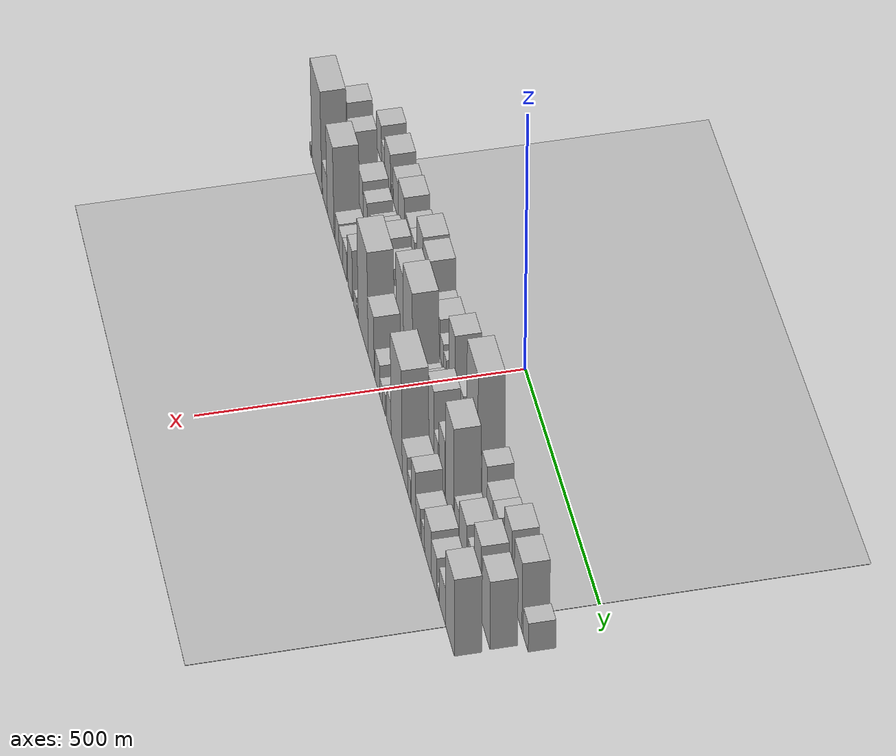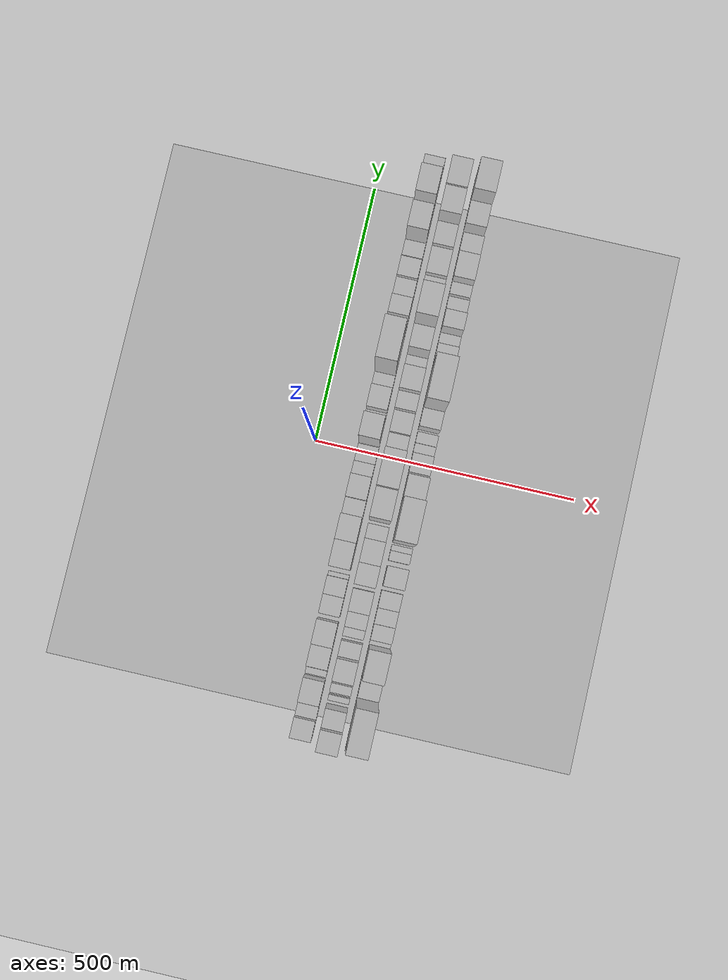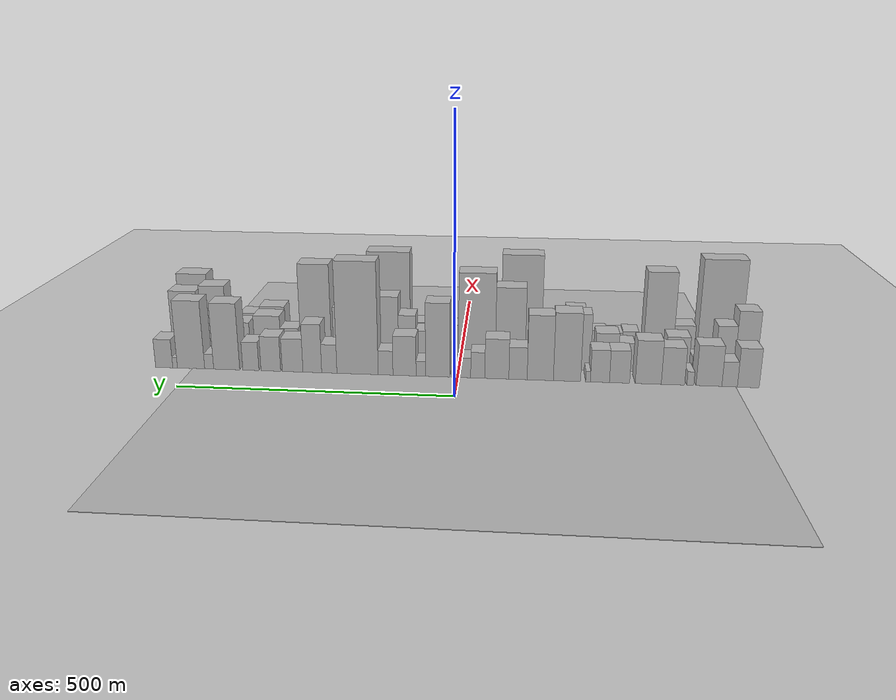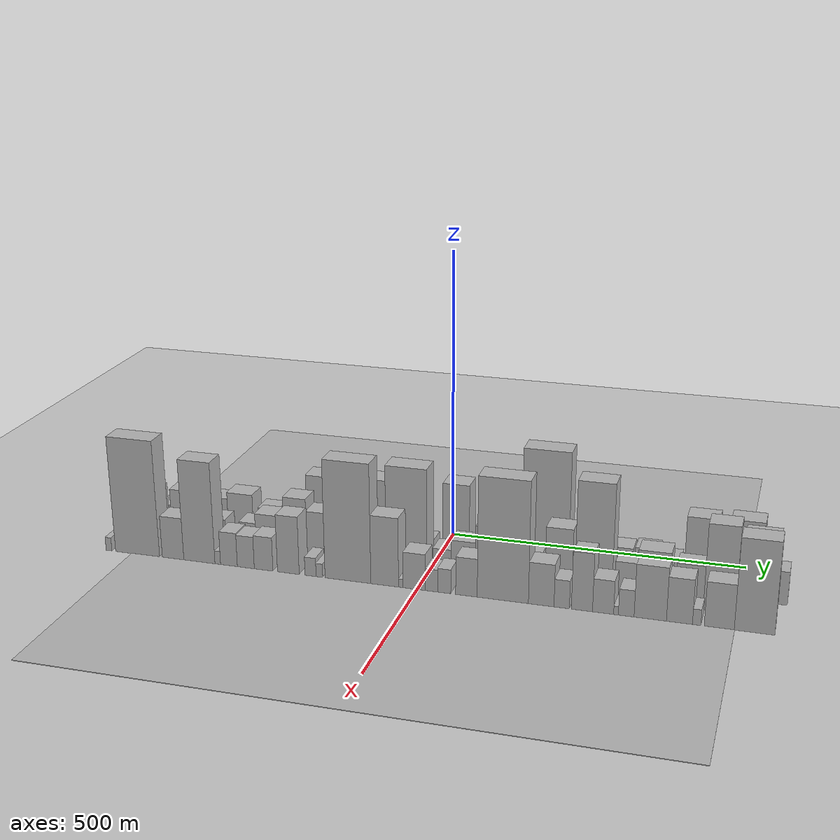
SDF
<?xml version="1.0" encoding="utf-8"?>

<sdf version="1.6">

   <world name="default">

      <gui fullscreen="0">

         <camera name="user_camera">

            <pose>-15 0 4.57585 0 0 0</pose>

            <view_controller>orbit</view_controller>

         </camera>

      </gui>

      <scene>

         <sky>

           <clouds>

             <speed>12</speed>

           </clouds>

         </sky>

         <ambient>0.4 0.4 0.4 1</ambient>

         <background>0.7 0.7 0.7 1</background>

         <shadows>1</shadows>

      </scene>

      <gravity>0 0 -9.8066</gravity>

      <magnetic_field>6e-06 2.3e-05 -4.2e-05</magnetic_field>

      <physics default="0" name="default_physics" type="ode">

         <ode>

            <solver>

               <type>quick</type>

               <iters>10</iters>

               <sor>1.0</sor>

               <use_dynamic_moi_rescaling>0</use_dynamic_moi_rescaling>

            </solver>

            <constraints>

               <cfm>0</cfm>

               <erp>0.2</erp>

               <contact_max_correcting_vel>100</contact_max_correcting_vel>

               <contact_surface_layer>0.001</contact_surface_layer>

            </constraints>

         </ode>

         <max_step_size>0.004</max_step_size>

         <real_time_factor>1</real_time_factor>

         <real_time_update_rate>250</real_time_update_rate>

      </physics>

      <light name="sun" type="directional">

         <cast_shadows>1</cast_shadows>

         <pose>0 0 10 0 0 0</pose>

         <diffuse>0.8 0.8 0.8 1</diffuse>

         <specular>0.2 0.2 0.2 1</specular>

         <attenuation>

            <range>1000</range>

            <constant>0.9</constant>

            <linear>0.01</linear>

            <quadratic>0.001</quadratic>

         </attenuation>

         <direction>-0.5 0.1 -0.9</direction>

      </light>

      <include>

         <name>ground_plane_1</name>

         <uri>model://HANNAS_ground_plane</uri>

         <pose>0 0 0  0 0 0</pose>

      </include>

      <include>

         <name>ground_plane_2</name>

         <uri>model://HANNAS_ground_plane</uri>

         <pose>100 0 0  0 0 0</pose>

      </include>

      <model name="building_1">

         <static>1</static>

         <pose frame="">100.0000 -521.8874 0 0.000000 0.000000 0.000000</pose>

         <link name="link">

            <pose frame="">0 0 37.50 0 0 0</pose>

            <collision name="collision">

               <geometry>

                  <box>

                     <size>40.0000 38.2253 75.0000</size>

                  </box>

               </geometry>

               <max_contacts>10</max_contacts>

               <surface>

                  <contact>

                     <ode/>

                  </contact>

                  <bounce/>

                  <friction>

                     <torsional>

                        <ode/>

                     </torsional>

                     <ode/>

                  </friction>

               </surface>

            </collision>

            <visual name="visual">

               <cast_shadows>0</cast_shadows>

               <geometry>

                  <box>

                     <size>40.0000 38.2253 75.0000</size>

                  </box>

               </geometry>

               <material>

                  <script>

                     <uri>model://HANNAS_wall/materials/scripts</uri>

                     <uri>model://HANNAS_wall/materials/textures</uri>

                     <name>vrc/HANNAS_wall</name>

                  </script>

               </material>

            </visual>

            <self_collide>0</self_collide>

            <enable_wind>0</enable_wind>

            <kinematic>0</kinematic>

         </link>

      </model>

      <model name="building_2">

         <static>1</static>

         <pose frame="">100.0000 -489.1310 0 0.000000 0.000000 0.000000</pose>

         <link name="link">

            <pose frame="">0 0 24.00 0 0 0</pose>

            <collision name="collision">

               <geometry>

                  <box>

                     <size>40.0000 27.2876 48.0000</size>

                  </box>

               </geometry>

               <max_contacts>10</max_contacts>

               <surface>

                  <contact>

                     <ode/>

                  </contact>

                  <bounce/>

                  <friction>

                     <torsional>

                        <ode/>

                     </torsional>

                     <ode/>

                  </friction>

               </surface>

            </collision>

            <visual name="visual">

               <cast_shadows>0</cast_shadows>

               <geometry>

                  <box>

                     <size>40.0000 27.2876 48.0000</size>

                  </box>

               </geometry>

               <material>

                  <script>

                     <uri>model://HANNAS_wall/materials/scripts</uri>

                     <uri>model://HANNAS_wall/materials/textures</uri>

                     <name>vrc/HANNAS_wall</name>

                  </script>

               </material>

            </visual>

            <self_collide>0</self_collide>

            <enable_wind>0</enable_wind>

            <kinematic>0</kinematic>

         </link>

      </model>

      <model name="building_3">

         <static>1</static>

         <pose frame="">100.0000 -452.7695 0 0.000000 0.000000 0.000000</pose>

         <link name="link">

            <pose frame="">0 0 39.00 0 0 0</pose>

            <collision name="collision">

               <geometry>

                  <box>

                     <size>40.0000 45.4354 78.0000</size>

                  </box>

               </geometry>

               <max_contacts>10</max_contacts>

               <surface>

                  <contact>

                     <ode/>

                  </contact>

                  <bounce/>

                  <friction>

                     <torsional>

                        <ode/>

                     </torsional>

                     <ode/>

                  </friction>

               </surface>

            </collision>

            <visual name="visual">

               <cast_shadows>0</cast_shadows>

               <geometry>

                  <box>

                     <size>40.0000 45.4354 78.0000</size>

                  </box>

               </geometry>

               <material>

                  <script>

                     <uri>model://HANNAS_wall/materials/scripts</uri>

                     <uri>model://HANNAS_wall/materials/textures</uri>

                     <name>vrc/HANNAS_wall</name>

                  </script>

               </material>

            </visual>

            <self_collide>0</self_collide>

            <enable_wind>0</enable_wind>

            <kinematic>0</kinematic>

         </link>

      </model>

      <model name="building_4">

         <static>1</static>

         <pose frame="">100.0000 -419.9362 0 0.000000 0.000000 0.000000</pose>

         <link name="link">

            <pose frame="">0 0 13.50 0 0 0</pose>

            <collision name="collision">

               <geometry>

                  <box>

                     <size>40.0000 12.2310 27.0000</size>

                  </box>

               </geometry>

               <max_contacts>10</max_contacts>

               <surface>

                  <contact>

                     <ode/>

                  </contact>

                  <bounce/>

                  <friction>

                     <torsional>

                        <ode/>

                     </torsional>

                     <ode/>

                  </friction>

               </surface>

            </collision>

            <visual name="visual">

               <cast_shadows>0</cast_shadows>

               <geometry>

                  <box>

                     <size>40.0000 12.2310 27.0000</size>

                  </box>

               </geometry>

               <material>

                  <script>

                     <uri>model://HANNAS_wall/materials/scripts</uri>

                     <uri>model://HANNAS_wall/materials/textures</uri>

                     <name>vrc/HANNAS_wall</name>

                  </script>

               </material>

            </visual>

            <self_collide>0</self_collide>

            <enable_wind>0</enable_wind>

            <kinematic>0</kinematic>

         </link>

      </model>

      <model name="building_5">

         <static>1</static>

         <pose frame="">100.0000 -389.0975 0 0.000000 0.000000 0.000000</pose>

         <link name="link">

            <pose frame="">0 0 36.00 0 0 0</pose>

            <collision name="collision">

               <geometry>

                  <box>

                     <size>40.0000 41.4465 72.0000</size>

                  </box>

               </geometry>

               <max_contacts>10</max_contacts>

               <surface>

                  <contact>

                     <ode/>

                  </contact>

                  <bounce/>

                  <friction>

                     <torsional>

                        <ode/>

                     </torsional>

                     <ode/>

                  </friction>

               </surface>

            </collision>

            <visual name="visual">

               <cast_shadows>0</cast_shadows>

               <geometry>

                  <box>

                     <size>40.0000 41.4465 72.0000</size>

                  </box>

               </geometry>

               <material>

                  <script>

                     <uri>model://HANNAS_wall/materials/scripts</uri>

                     <uri>model://HANNAS_wall/materials/textures</uri>

                     <name>vrc/HANNAS_wall</name>

                  </script>

               </material>

            </visual>

            <self_collide>0</self_collide>

            <enable_wind>0</enable_wind>

            <kinematic>0</kinematic>

         </link>

      </model>

      <model name="building_6">

         <static>1</static>

         <pose frame="">100.0000 -345.1683 0 0.000000 0.000000 0.000000</pose>

         <link name="link">

            <pose frame="">0 0 42.00 0 0 0</pose>

            <collision name="collision">

               <geometry>

                  <box>

                     <size>40.0000 46.4119 84.0000</size>

                  </box>

               </geometry>

               <max_contacts>10</max_contacts>

               <surface>

                  <contact>

                     <ode/>

                  </contact>

                  <bounce/>

                  <friction>

                     <torsional>

                        <ode/>

                     </torsional>

                     <ode/>

                  </friction>

               </surface>

            </collision>

            <visual name="visual">

               <cast_shadows>0</cast_shadows>

               <geometry>

                  <box>

                     <size>40.0000 46.4119 84.0000</size>

                  </box>

               </geometry>

               <material>

                  <script>

                     <uri>model://HANNAS_wall/materials/scripts</uri>

                     <uri>model://HANNAS_wall/materials/textures</uri>

                     <name>vrc/HANNAS_wall</name>

                  </script>

               </material>

            </visual>

            <self_collide>0</self_collide>

            <enable_wind>0</enable_wind>

            <kinematic>0</kinematic>

         </link>

      </model>

      <model name="building_7">

         <static>1</static>

         <pose frame="">100.0000 -293.8474 0 0.000000 0.000000 0.000000</pose>

         <link name="link">

            <pose frame="">0 0 31.50 0 0 0</pose>

            <collision name="collision">

               <geometry>

                  <box>

                     <size>40.0000 36.2299 63.0000</size>

                  </box>

               </geometry>

               <max_contacts>10</max_contacts>

               <surface>

                  <contact>

                     <ode/>

                  </contact>

                  <bounce/>

                  <friction>

                     <torsional>

                        <ode/>

                     </torsional>

                     <ode/>

                  </friction>

               </surface>

            </collision>

            <visual name="visual">

               <cast_shadows>0</cast_shadows>

               <geometry>

                  <box>

                     <size>40.0000 36.2299 63.0000</size>

                  </box>

               </geometry>

               <material>

                  <script>

                     <uri>model://HANNAS_wall/materials/scripts</uri>

                     <uri>model://HANNAS_wall/materials/textures</uri>

                     <name>vrc/HANNAS_wall</name>

                  </script>

               </material>

            </visual>

            <self_collide>0</self_collide>

            <enable_wind>0</enable_wind>

            <kinematic>0</kinematic>

         </link>

      </model>

      <model name="building_8">

         <static>1</static>

         <pose frame="">100.0000 -258.6366 0 0.000000 0.000000 0.000000</pose>

         <link name="link">

            <pose frame="">0 0 31.50 0 0 0</pose>

            <collision name="collision">

               <geometry>

                  <box>

                     <size>40.0000 34.1916 63.0000</size>

                  </box>

               </geometry>

               <max_contacts>10</max_contacts>

               <surface>

                  <contact>

                     <ode/>

                  </contact>

                  <bounce/>

                  <friction>

                     <torsional>

                        <ode/>

                     </torsional>

                     <ode/>

                  </friction>

               </surface>

            </collision>

            <visual name="visual">

               <cast_shadows>0</cast_shadows>

               <geometry>

                  <box>

                     <size>40.0000 34.1916 63.0000</size>

                  </box>

               </geometry>

               <material>

                  <script>

                     <uri>model://HANNAS_wall/materials/scripts</uri>

                     <uri>model://HANNAS_wall/materials/textures</uri>

                     <name>vrc/HANNAS_wall</name>

                  </script>

               </material>

            </visual>

            <self_collide>0</self_collide>

            <enable_wind>0</enable_wind>

            <kinematic>0</kinematic>

         </link>

      </model>

      <model name="building_9">

         <static>1</static>

         <pose frame="">100.0000 -237.2392 0 0.000000 0.000000 0.000000</pose>

         <link name="link">

            <pose frame="">0 0 10.50 0 0 0</pose>

            <collision name="collision">

               <geometry>

                  <box>

                     <size>40.0000 8.6033 21.0000</size>

                  </box>

               </geometry>

               <max_contacts>10</max_contacts>

               <surface>

                  <contact>

                     <ode/>

                  </contact>

                  <bounce/>

                  <friction>

                     <torsional>

                        <ode/>

                     </torsional>

                     <ode/>

                  </friction>

               </surface>

            </collision>

            <visual name="visual">

               <cast_shadows>0</cast_shadows>

               <geometry>

                  <box>

                     <size>40.0000 8.6033 21.0000</size>

                  </box>

               </geometry>

               <material>

                  <script>

                     <uri>model://HANNAS_wall/materials/scripts</uri>

                     <uri>model://HANNAS_wall/materials/textures</uri>

                     <name>vrc/HANNAS_wall</name>

                  </script>

               </material>

            </visual>

            <self_collide>0</self_collide>

            <enable_wind>0</enable_wind>

            <kinematic>0</kinematic>

         </link>

      </model>

      <model name="building_10">

         <static>1</static>

         <pose frame="">100.0000 -199.2815 0 0.000000 0.000000 0.000000</pose>

         <link name="link">

            <pose frame="">0 0 66.00 0 0 0</pose>

            <collision name="collision">

               <geometry>

                  <box>

                     <size>40.0000 49.3121 132.0000</size>

                  </box>

               </geometry>

               <max_contacts>10</max_contacts>

               <surface>

                  <contact>

                     <ode/>

                  </contact>

                  <bounce/>

                  <friction>

                     <torsional>

                        <ode/>

                     </torsional>

                     <ode/>

                  </friction>

               </surface>

            </collision>

            <visual name="visual">

               <cast_shadows>0</cast_shadows>

               <geometry>

                  <box>

                     <size>40.0000 49.3121 132.0000</size>

                  </box>

               </geometry>

               <material>

                  <script>

                     <uri>model://HANNAS_wall/materials/scripts</uri>

                     <uri>model://HANNAS_wall/materials/textures</uri>

                     <name>vrc/HANNAS_wall</name>

                  </script>

               </material>

            </visual>

            <self_collide>0</self_collide>

            <enable_wind>0</enable_wind>

            <kinematic>0</kinematic>

         </link>

      </model>

      <model name="building_11">

         <static>1</static>

         <pose frame="">100.0000 -150.8150 0 0.000000 0.000000 0.000000</pose>

         <link name="link">

            <pose frame="">0 0 63.00 0 0 0</pose>

            <collision name="collision">

               <geometry>

                  <box>

                     <size>40.0000 47.6210 126.0000</size>

                  </box>

               </geometry>

               <max_contacts>10</max_contacts>

               <surface>

                  <contact>

                     <ode/>

                  </contact>

                  <bounce/>

                  <friction>

                     <torsional>

                        <ode/>

                     </torsional>

                     <ode/>

                  </friction>

               </surface>

            </collision>

            <visual name="visual">

               <cast_shadows>0</cast_shadows>

               <geometry>

                  <box>

                     <size>40.0000 47.6210 126.0000</size>

                  </box>

               </geometry>

               <material>

                  <script>

                     <uri>model://HANNAS_wall/materials/scripts</uri>

                     <uri>model://HANNAS_wall/materials/textures</uri>

                     <name>vrc/HANNAS_wall</name>

                  </script>

               </material>

            </visual>

            <self_collide>0</self_collide>

            <enable_wind>0</enable_wind>

            <kinematic>0</kinematic>

         </link>

      </model>

      <model name="building_12">

         <static>1</static>

         <pose frame="">100.0000 -110.3735 0 0.000000 0.000000 0.000000</pose>

         <link name="link">

            <pose frame="">0 0 31.50 0 0 0</pose>

            <collision name="collision">

               <geometry>

                  <box>

                     <size>40.0000 33.2620 63.0000</size>

                  </box>

               </geometry>

               <max_contacts>10</max_contacts>

               <surface>

                  <contact>

                     <ode/>

                  </contact>

                  <bounce/>

                  <friction>

                     <torsional>

                        <ode/>

                     </torsional>

                     <ode/>

                  </friction>

               </surface>

            </collision>

            <visual name="visual">

               <cast_shadows>0</cast_shadows>

               <geometry>

                  <box>

                     <size>40.0000 33.2620 63.0000</size>

                  </box>

               </geometry>

               <material>

                  <script>

                     <uri>model://HANNAS_wall/materials/scripts</uri>

                     <uri>model://HANNAS_wall/materials/textures</uri>

                     <name>vrc/HANNAS_wall</name>

                  </script>

               </material>

            </visual>

            <self_collide>0</self_collide>

            <enable_wind>0</enable_wind>

            <kinematic>0</kinematic>

         </link>

      </model>

      <model name="building_13">

         <static>1</static>

         <pose frame="">100.0000 -71.7717 0 0.000000 0.000000 0.000000</pose>

         <link name="link">

            <pose frame="">0 0 39.00 0 0 0</pose>

            <collision name="collision">

               <geometry>

                  <box>

                     <size>40.0000 43.9417 78.0000</size>

                  </box>

               </geometry>

               <max_contacts>10</max_contacts>

               <surface>

                  <contact>

                     <ode/>

                  </contact>

                  <bounce/>

                  <friction>

                     <torsional>

                        <ode/>

                     </torsional>

                     <ode/>

                  </friction>

               </surface>

            </collision>

            <visual name="visual">

               <cast_shadows>0</cast_shadows>

               <geometry>

                  <box>

                     <size>40.0000 43.9417 78.0000</size>

                  </box>

               </geometry>

               <material>

                  <script>

                     <uri>model://HANNAS_wall/materials/scripts</uri>

                     <uri>model://HANNAS_wall/materials/textures</uri>

                     <name>vrc/HANNAS_wall</name>

                  </script>

               </material>

            </visual>

            <self_collide>0</self_collide>

            <enable_wind>0</enable_wind>

            <kinematic>0</kinematic>

         </link>

      </model>

      <model name="building_14">

         <static>1</static>

         <pose frame="">100.0000 -36.7767 0 0.000000 0.000000 0.000000</pose>

         <link name="link">

            <pose frame="">0 0 25.50 0 0 0</pose>

            <collision name="collision">

               <geometry>

                  <box>

                     <size>40.0000 26.0483 51.0000</size>

                  </box>

               </geometry>

               <max_contacts>10</max_contacts>

               <surface>

                  <contact>

                     <ode/>

                  </contact>

                  <bounce/>

                  <friction>

                     <torsional>

                        <ode/>

                     </torsional>

                     <ode/>

                  </friction>

               </surface>

            </collision>

            <visual name="visual">

               <cast_shadows>0</cast_shadows>

               <geometry>

                  <box>

                     <size>40.0000 26.0483 51.0000</size>

                  </box>

               </geometry>

               <material>

                  <script>

                     <uri>model://HANNAS_wall/materials/scripts</uri>

                     <uri>model://HANNAS_wall/materials/textures</uri>

                     <name>vrc/HANNAS_wall</name>

                  </script>

               </material>

            </visual>

            <self_collide>0</self_collide>

            <enable_wind>0</enable_wind>

            <kinematic>0</kinematic>

         </link>

      </model>

      <model name="building_15">

         <static>1</static>

         <pose frame="">100.0000 -12.8435 0 0.000000 0.000000 0.000000</pose>

         <link name="link">

            <pose frame="">0 0 19.50 0 0 0</pose>

            <collision name="collision">

               <geometry>

                  <box>

                     <size>40.0000 21.8180 39.0000</size>

                  </box>

               </geometry>

               <max_contacts>10</max_contacts>

               <surface>

                  <contact>

                     <ode/>

                  </contact>

                  <bounce/>

                  <friction>

                     <torsional>

                        <ode/>

                     </torsional>

                     <ode/>

                  </friction>

               </surface>

            </collision>

            <visual name="visual">

               <cast_shadows>0</cast_shadows>

               <geometry>

                  <box>

                     <size>40.0000 21.8180 39.0000</size>

                  </box>

               </geometry>

               <material>

                  <script>

                     <uri>model://HANNAS_wall/materials/scripts</uri>

                     <uri>model://HANNAS_wall/materials/textures</uri>

                     <name>vrc/HANNAS_wall</name>

                  </script>

               </material>

            </visual>

            <self_collide>0</self_collide>

            <enable_wind>0</enable_wind>

            <kinematic>0</kinematic>

         </link>

      </model>

      <model name="building_16">

         <static>1</static>

         <pose frame="">100.0000 6.3810 0 0.000000 0.000000 0.000000</pose>

         <link name="link">

            <pose frame="">0 0 12.00 0 0 0</pose>

            <collision name="collision">

               <geometry>

                  <box>

                     <size>40.0000 10.6311 24.0000</size>

                  </box>

               </geometry>

               <max_contacts>10</max_contacts>

               <surface>

                  <contact>

                     <ode/>

                  </contact>

                  <bounce/>

                  <friction>

                     <torsional>

                        <ode/>

                     </torsional>

                     <ode/>

                  </friction>

               </surface>

            </collision>

            <visual name="visual">

               <cast_shadows>0</cast_shadows>

               <geometry>

                  <box>

                     <size>40.0000 10.6311 24.0000</size>

                  </box>

               </geometry>

               <material>

                  <script>

                     <uri>model://HANNAS_wall/materials/scripts</uri>

                     <uri>model://HANNAS_wall/materials/textures</uri>

                     <name>vrc/HANNAS_wall</name>

                  </script>

               </material>

            </visual>

            <self_collide>0</self_collide>

            <enable_wind>0</enable_wind>

            <kinematic>0</kinematic>

         </link>

      </model>

      <model name="building_17">

         <static>1</static>

         <pose frame="">100.0000 37.1451 0 0.000000 0.000000 0.000000</pose>

         <link name="link">

            <pose frame="">0 0 72.00 0 0 0</pose>

            <collision name="collision">

               <geometry>

                  <box>

                     <size>40.0000 44.8969 144.0000</size>

                  </box>

               </geometry>

               <max_contacts>10</max_contacts>

               <surface>

                  <contact>

                     <ode/>

                  </contact>

                  <bounce/>

                  <friction>

                     <torsional>

                        <ode/>

                     </torsional>

                     <ode/>

                  </friction>

               </surface>

            </collision>

            <visual name="visual">

               <cast_shadows>0</cast_shadows>

               <geometry>

                  <box>

                     <size>40.0000 44.8969 144.0000</size>

                  </box>

               </geometry>

               <material>

                  <script>

                     <uri>model://HANNAS_wall/materials/scripts</uri>

                     <uri>model://HANNAS_wall/materials/textures</uri>

                     <name>vrc/HANNAS_wall</name>

                  </script>

               </material>

            </visual>

            <self_collide>0</self_collide>

            <enable_wind>0</enable_wind>

            <kinematic>0</kinematic>

         </link>

      </model>

      <model name="building_18">

         <static>1</static>

         <pose frame="">100.0000 68.3640 0 0.000000 0.000000 0.000000</pose>

         <link name="link">

            <pose frame="">0 0 15.00 0 0 0</pose>

            <collision name="collision">

               <geometry>

                  <box>

                     <size>40.0000 17.5411 30.0000</size>

                  </box>

               </geometry>

               <max_contacts>10</max_contacts>

               <surface>

                  <contact>

                     <ode/>

                  </contact>

                  <bounce/>

                  <friction>

                     <torsional>

                        <ode/>

                     </torsional>

                     <ode/>

                  </friction>

               </surface>

            </collision>

            <visual name="visual">

               <cast_shadows>0</cast_shadows>

               <geometry>

                  <box>

                     <size>40.0000 17.5411 30.0000</size>

                  </box>

               </geometry>

               <material>

                  <script>

                     <uri>model://HANNAS_wall/materials/scripts</uri>

                     <uri>model://HANNAS_wall/materials/textures</uri>

                     <name>vrc/HANNAS_wall</name>

                  </script>

               </material>

            </visual>

            <self_collide>0</self_collide>

            <enable_wind>0</enable_wind>

            <kinematic>0</kinematic>

         </link>

      </model>

      <model name="building_19">

         <static>1</static>

         <pose frame="">100.0000 98.6439 0 0.000000 0.000000 0.000000</pose>

         <link name="link">

            <pose frame="">0 0 39.00 0 0 0</pose>

            <collision name="collision">

               <geometry>

                  <box>

                     <size>40.0000 43.0187 78.0000</size>

                  </box>

               </geometry>

               <max_contacts>10</max_contacts>

               <surface>

                  <contact>

                     <ode/>

                  </contact>

                  <bounce/>

                  <friction>

                     <torsional>

                        <ode/>

                     </torsional>

                     <ode/>

                  </friction>

               </surface>

            </collision>

            <visual name="visual">

               <cast_shadows>0</cast_shadows>

               <geometry>

                  <box>

                     <size>40.0000 43.0187 78.0000</size>

                  </box>

               </geometry>

               <material>

                  <script>

                     <uri>model://HANNAS_wall/materials/scripts</uri>

                     <uri>model://HANNAS_wall/materials/textures</uri>

                     <name>vrc/HANNAS_wall</name>

                  </script>

               </material>

            </visual>

            <self_collide>0</self_collide>

            <enable_wind>0</enable_wind>

            <kinematic>0</kinematic>

         </link>

      </model>

      <model name="building_20">

         <static>1</static>

         <pose frame="">100.0000 133.8845 0 0.000000 0.000000 0.000000</pose>

         <link name="link">

            <pose frame="">0 0 24.00 0 0 0</pose>

            <collision name="collision">

               <geometry>

                  <box>

                     <size>40.0000 27.4626 48.0000</size>

                  </box>

               </geometry>

               <max_contacts>10</max_contacts>

               <surface>

                  <contact>

                     <ode/>

                  </contact>

                  <bounce/>

                  <friction>

                     <torsional>

                        <ode/>

                     </torsional>

                     <ode/>

                  </friction>

               </surface>

            </collision>

            <visual name="visual">

               <cast_shadows>0</cast_shadows>

               <geometry>

                  <box>

                     <size>40.0000 27.4626 48.0000</size>

                  </box>

               </geometry>

               <material>

                  <script>

                     <uri>model://HANNAS_wall/materials/scripts</uri>

                     <uri>model://HANNAS_wall/materials/textures</uri>

                     <name>vrc/HANNAS_wall</name>

                  </script>

               </material>

            </visual>

            <self_collide>0</self_collide>

            <enable_wind>0</enable_wind>

            <kinematic>0</kinematic>

         </link>

      </model>

      <model name="building_21">

         <static>1</static>

         <pose frame="">100.0000 186.3772 0 0.000000 0.000000 0.000000</pose>

         <link name="link">

            <pose frame="">0 0 109.50 0 0 0</pose>

            <collision name="collision">

               <geometry>

                  <box>

                     <size>40.0000 77.5228 219.0000</size>

                  </box>

               </geometry>

               <max_contacts>10</max_contacts>

               <surface>

                  <contact>

                     <ode/>

                  </contact>

                  <bounce/>

                  <friction>

                     <torsional>

                        <ode/>

                     </torsional>

                     <ode/>

                  </friction>

               </surface>

            </collision>

            <visual name="visual">

               <cast_shadows>0</cast_shadows>

               <geometry>

                  <box>

                     <size>40.0000 77.5228 219.0000</size>

                  </box>

               </geometry>

               <material>

                  <script>

                     <uri>model://HANNAS_wall/materials/scripts</uri>

                     <uri>model://HANNAS_wall/materials/textures</uri>

                     <name>vrc/HANNAS_wall</name>

                  </script>

               </material>

            </visual>

            <self_collide>0</self_collide>

            <enable_wind>0</enable_wind>

            <kinematic>0</kinematic>

         </link>

      </model>

      <model name="building_22">

         <static>1</static>

         <pose frame="">100.0000 239.5046 0 0.000000 0.000000 0.000000</pose>

         <link name="link">

            <pose frame="">0 0 28.50 0 0 0</pose>

            <collision name="collision">

               <geometry>

                  <box>

                     <size>40.0000 28.7320 57.0000</size>

                  </box>

               </geometry>

               <max_contacts>10</max_contacts>

               <surface>

                  <contact>

                     <ode/>

                  </contact>

                  <bounce/>

                  <friction>

                     <torsional>

                        <ode/>

                     </torsional>

                     <ode/>

                  </friction>

               </surface>

            </collision>

            <visual name="visual">

               <cast_shadows>0</cast_shadows>

               <geometry>

                  <box>

                     <size>40.0000 28.7320 57.0000</size>

                  </box>

               </geometry>

               <material>

                  <script>

                     <uri>model://HANNAS_wall/materials/scripts</uri>

                     <uri>model://HANNAS_wall/materials/textures</uri>

                     <name>vrc/HANNAS_wall</name>

                  </script>

               </material>

            </visual>

            <self_collide>0</self_collide>

            <enable_wind>0</enable_wind>

            <kinematic>0</kinematic>

         </link>

      </model>

      <model name="building_23">

         <static>1</static>

         <pose frame="">100.0000 271.5599 0 0.000000 0.000000 0.000000</pose>

         <link name="link">

            <pose frame="">0 0 48.00 0 0 0</pose>

            <collision name="collision">

               <geometry>

                  <box>

                     <size>40.0000 35.3786 96.0000</size>

                  </box>

               </geometry>

               <max_contacts>10</max_contacts>

               <surface>

                  <contact>

                     <ode/>

                  </contact>

                  <bounce/>

                  <friction>

                     <torsional>

                        <ode/>

                     </torsional>

                     <ode/>

                  </friction>

               </surface>

            </collision>

            <visual name="visual">

               <cast_shadows>0</cast_shadows>

               <geometry>

                  <box>

                     <size>40.0000 35.3786 96.0000</size>

                  </box>

               </geometry>

               <material>

                  <script>

                     <uri>model://HANNAS_wall/materials/scripts</uri>

                     <uri>model://HANNAS_wall/materials/textures</uri>

                     <name>vrc/HANNAS_wall</name>

                  </script>

               </material>

            </visual>

            <self_collide>0</self_collide>

            <enable_wind>0</enable_wind>

            <kinematic>0</kinematic>

         </link>

      </model>

      <model name="building_24">

         <static>1</static>

         <pose frame="">100.0000 308.8940 0 0.000000 0.000000 0.000000</pose>

         <link name="link">

            <pose frame="">0 0 33.00 0 0 0</pose>

            <collision name="collision">

               <geometry>

                  <box>

                     <size>40.0000 39.2897 66.0000</size>

                  </box>

               </geometry>

               <max_contacts>10</max_contacts>

               <surface>

                  <contact>

                     <ode/>

                  </contact>

                  <bounce/>

                  <friction>

                     <torsional>

                        <ode/>

                     </torsional>

                     <ode/>

                  </friction>

               </surface>

            </collision>

            <visual name="visual">

               <cast_shadows>0</cast_shadows>

               <geometry>

                  <box>

                     <size>40.0000 39.2897 66.0000</size>

                  </box>

               </geometry>

               <material>

                  <script>

                     <uri>model://HANNAS_wall/materials/scripts</uri>

                     <uri>model://HANNAS_wall/materials/textures</uri>

                     <name>vrc/HANNAS_wall</name>

                  </script>

               </material>

            </visual>

            <self_collide>0</self_collide>

            <enable_wind>0</enable_wind>

            <kinematic>0</kinematic>

         </link>

      </model>

      <model name="building_25">

         <static>1</static>

         <pose frame="">100.0000 350.2658 0 0.000000 0.000000 0.000000</pose>

         <link name="link">

            <pose frame="">0 0 34.50 0 0 0</pose>

            <collision name="collision">

               <geometry>

                  <box>

                     <size>40.0000 37.4539 69.0000</size>

                  </box>

               </geometry>

               <max_contacts>10</max_contacts>

               <surface>

                  <contact>

                     <ode/>

                  </contact>

                  <bounce/>

                  <friction>

                     <torsional>

                        <ode/>

                     </torsional>

                     <ode/>

                  </friction>

               </surface>

            </collision>

            <visual name="visual">

               <cast_shadows>0</cast_shadows>

               <geometry>

                  <box>

                     <size>40.0000 37.4539 69.0000</size>

                  </box>

               </geometry>

               <material>

                  <script>

                     <uri>model://HANNAS_wall/materials/scripts</uri>

                     <uri>model://HANNAS_wall/materials/textures</uri>

                     <name>vrc/HANNAS_wall</name>

                  </script>

               </material>

            </visual>

            <self_collide>0</self_collide>

            <enable_wind>0</enable_wind>

            <kinematic>0</kinematic>

         </link>

      </model>

      <model name="building_26">

         <static>1</static>

         <pose frame="">100.0000 388.3803 0 0.000000 0.000000 0.000000</pose>

         <link name="link">

            <pose frame="">0 0 28.50 0 0 0</pose>

            <collision name="collision">

               <geometry>

                  <box>

                     <size>40.0000 30.7751 57.0000</size>

                  </box>

               </geometry>

               <max_contacts>10</max_contacts>

               <surface>

                  <contact>

                     <ode/>

                  </contact>

                  <bounce/>

                  <friction>

                     <torsional>

                        <ode/>

                     </torsional>

                     <ode/>

                  </friction>

               </surface>

            </collision>

            <visual name="visual">

               <cast_shadows>0</cast_shadows>

               <geometry>

                  <box>

                     <size>40.0000 30.7751 57.0000</size>

                  </box>

               </geometry>

               <material>

                  <script>

                     <uri>model://HANNAS_wall/materials/scripts</uri>

                     <uri>model://HANNAS_wall/materials/textures</uri>

                     <name>vrc/HANNAS_wall</name>

                  </script>

               </material>

            </visual>

            <self_collide>0</self_collide>

            <enable_wind>0</enable_wind>

            <kinematic>0</kinematic>

         </link>

      </model>

      <model name="building_27">

         <static>1</static>

         <pose frame="">100.0000 434.8495 0 0.000000 0.000000 0.000000</pose>

         <link name="link">

            <pose frame="">0 0 66.00 0 0 0</pose>

            <collision name="collision">

               <geometry>

                  <box>

                     <size>40.0000 50.1632 132.0000</size>

                  </box>

               </geometry>

               <max_contacts>10</max_contacts>

               <surface>

                  <contact>

                     <ode/>

                  </contact>

                  <bounce/>

                  <friction>

                     <torsional>

                        <ode/>

                     </torsional>

                     <ode/>

                  </friction>

               </surface>

            </collision>

            <visual name="visual">

               <cast_shadows>0</cast_shadows>

               <geometry>

                  <box>

                     <size>40.0000 50.1632 132.0000</size>

                  </box>

               </geometry>

               <material>

                  <script>

                     <uri>model://HANNAS_wall/materials/scripts</uri>

                     <uri>model://HANNAS_wall/materials/textures</uri>

                     <name>vrc/HANNAS_wall</name>

                  </script>

               </material>

            </visual>

            <self_collide>0</self_collide>

            <enable_wind>0</enable_wind>

            <kinematic>0</kinematic>

         </link>

      </model>

      <model name="building_28">

         <static>1</static>

         <pose frame="">100.0000 468.5543 0 0.000000 0.000000 0.000000</pose>

         <link name="link">

            <pose frame="">0 0 15.00 0 0 0</pose>

            <collision name="collision">

               <geometry>

                  <box>

                     <size>40.0000 17.2466 30.0000</size>

                  </box>

               </geometry>

               <max_contacts>10</max_contacts>

               <surface>

                  <contact>

                     <ode/>

                  </contact>

                  <bounce/>

                  <friction>

                     <torsional>

                        <ode/>

                     </torsional>

                     <ode/>

                  </friction>

               </surface>

            </collision>

            <visual name="visual">

               <cast_shadows>0</cast_shadows>

               <geometry>

                  <box>

                     <size>40.0000 17.2466 30.0000</size>

                  </box>

               </geometry>

               <material>

                  <script>

                     <uri>model://HANNAS_wall/materials/scripts</uri>

                     <uri>model://HANNAS_wall/materials/textures</uri>

                     <name>vrc/HANNAS_wall</name>

                  </script>

               </material>

            </visual>

            <self_collide>0</self_collide>

            <enable_wind>0</enable_wind>

            <kinematic>0</kinematic>

         </link>

      </model>

      <model name="building_29">

         <static>1</static>

         <pose frame="">100.0000 503.5258 0 0.000000 0.000000 0.000000</pose>

         <link name="link">

            <pose frame="">0 0 67.50 0 0 0</pose>

            <collision name="collision">

               <geometry>

                  <box>

                     <size>40.0000 52.6964 135.0000</size>

                  </box>

               </geometry>

               <max_contacts>10</max_contacts>

               <surface>

                  <contact>

                     <ode/>

                  </contact>

                  <bounce/>

                  <friction>

                     <torsional>

                        <ode/>

                     </torsional>

                     <ode/>

                  </friction>

               </surface>

            </collision>

            <visual name="visual">

               <cast_shadows>0</cast_shadows>

               <geometry>

                  <box>

                     <size>40.0000 52.6964 135.0000</size>

                  </box>

               </geometry>

               <material>

                  <script>

                     <uri>model://HANNAS_wall/materials/scripts</uri>

                     <uri>model://HANNAS_wall/materials/textures</uri>

                     <name>vrc/HANNAS_wall</name>

                  </script>

               </material>

            </visual>

            <self_collide>0</self_collide>

            <enable_wind>0</enable_wind>

            <kinematic>0</kinematic>

         </link>

      </model>

      <model name="building_30">

         <static>1</static>

         <pose frame="">100.0000 534.3964 0 0.000000 0.000000 0.000000</pose>

         <link name="link">

            <pose frame="">0 0 10.50 0 0 0</pose>

            <collision name="collision">

               <geometry>

                  <box>

                     <size>40.0000 9.0448 21.0000</size>

                  </box>

               </geometry>

               <max_contacts>10</max_contacts>

               <surface>

                  <contact>

                     <ode/>

                  </contact>

                  <bounce/>

                  <friction>

                     <torsional>

                        <ode/>

                     </torsional>

                     <ode/>

                  </friction>

               </surface>

            </collision>

            <visual name="visual">

               <cast_shadows>0</cast_shadows>

               <geometry>

                  <box>

                     <size>40.0000 9.0448 21.0000</size>

                  </box>

               </geometry>

               <material>

                  <script>

                     <uri>model://HANNAS_wall/materials/scripts</uri>

                     <uri>model://HANNAS_wall/materials/textures</uri>

                     <name>vrc/HANNAS_wall</name>

                  </script>

               </material>

            </visual>

            <self_collide>0</self_collide>

            <enable_wind>0</enable_wind>

            <kinematic>0</kinematic>

         </link>

      </model>

      <model name="building_31">

         <static>1</static>

         <pose frame="">100.0000 555.5444 0 0.000000 0.000000 0.000000</pose>

         <link name="link">

            <pose frame="">0 0 28.50 0 0 0</pose>

            <collision name="collision">

               <geometry>

                  <box>

                     <size>40.0000 33.2512 57.0000</size>

                  </box>

               </geometry>

               <max_contacts>10</max_contacts>

               <surface>

                  <contact>

                     <ode/>

                  </contact>

                  <bounce/>

                  <friction>

                     <torsional>

                        <ode/>

                     </torsional>

                     <ode/>

                  </friction>

               </surface>

            </collision>

            <visual name="visual">

               <cast_shadows>0</cast_shadows>

               <geometry>

                  <box>

                     <size>40.0000 33.2512 57.0000</size>

                  </box>

               </geometry>

               <material>

                  <script>

                     <uri>model://HANNAS_wall/materials/scripts</uri>

                     <uri>model://HANNAS_wall/materials/textures</uri>

                     <name>vrc/HANNAS_wall</name>

                  </script>

               </material>

            </visual>

            <self_collide>0</self_collide>

            <enable_wind>0</enable_wind>

            <kinematic>0</kinematic>

         </link>

      </model>

      <model name="building_32">

         <static>1</static>

         <pose frame="">152.0000 -528.0277 0 0.000000 0.000000 0.000000</pose>

         <link name="link">

            <pose frame="">0 0 63.00 0 0 0</pose>

            <collision name="collision">

               <geometry>

                  <box>

                     <size>40.0000 39.9446 126.0000</size>

                  </box>

               </geometry>

               <max_contacts>10</max_contacts>

               <surface>

                  <contact>

                     <ode/>

                  </contact>

                  <bounce/>

                  <friction>

                     <torsional>

                        <ode/>

                     </torsional>

                     <ode/>

                  </friction>

               </surface>

            </collision>

            <visual name="visual">

               <cast_shadows>0</cast_shadows>

               <geometry>

                  <box>

                     <size>40.0000 39.9446 126.0000</size>

                  </box>

               </geometry>

               <material>

                  <script>

                     <uri>model://HANNAS_wall/materials/scripts</uri>

                     <uri>model://HANNAS_wall/materials/textures</uri>

                     <name>vrc/HANNAS_wall</name>

                  </script>

               </material>

            </visual>

            <self_collide>0</self_collide>

            <enable_wind>0</enable_wind>

            <kinematic>0</kinematic>

         </link>

      </model>

      <model name="building_33">

         <static>1</static>

         <pose frame="">152.0000 -490.4714 0 0.000000 0.000000 0.000000</pose>

         <link name="link">

            <pose frame="">0 0 48.00 0 0 0</pose>

            <collision name="collision">

               <geometry>

                  <box>

                     <size>40.0000 35.1679 96.0000</size>

                  </box>

               </geometry>

               <max_contacts>10</max_contacts>

               <surface>

                  <contact>

                     <ode/>

                  </contact>

                  <bounce/>

                  <friction>

                     <torsional>

                        <ode/>

                     </torsional>

                     <ode/>

                  </friction>

               </surface>

            </collision>

            <visual name="visual">

               <cast_shadows>0</cast_shadows>

               <geometry>

                  <box>

                     <size>40.0000 35.1679 96.0000</size>

                  </box>

               </geometry>

               <material>

                  <script>

                     <uri>model://HANNAS_wall/materials/scripts</uri>

                     <uri>model://HANNAS_wall/materials/textures</uri>

                     <name>vrc/HANNAS_wall</name>

                  </script>

               </material>

            </visual>

            <self_collide>0</self_collide>

            <enable_wind>0</enable_wind>

            <kinematic>0</kinematic>

         </link>

      </model>

      <model name="building_34">

         <static>1</static>

         <pose frame="">152.0000 -459.4915 0 0.000000 0.000000 0.000000</pose>

         <link name="link">

            <pose frame="">0 0 12.00 0 0 0</pose>

            <collision name="collision">

               <geometry>

                  <box>

                     <size>40.0000 10.7919 24.0000</size>

                  </box>

               </geometry>

               <max_contacts>10</max_contacts>

               <surface>

                  <contact>

                     <ode/>

                  </contact>

                  <bounce/>

                  <friction>

                     <torsional>

                        <ode/>

                     </torsional>

                     <ode/>

                  </friction>

               </surface>

            </collision>

            <visual name="visual">

               <cast_shadows>0</cast_shadows>

               <geometry>

                  <box>

                     <size>40.0000 10.7919 24.0000</size>

                  </box>

               </geometry>

               <material>

                  <script>

                     <uri>model://HANNAS_wall/materials/scripts</uri>

                     <uri>model://HANNAS_wall/materials/textures</uri>

                     <name>vrc/HANNAS_wall</name>

                  </script>

               </material>

            </visual>

            <self_collide>0</self_collide>

            <enable_wind>0</enable_wind>

            <kinematic>0</kinematic>

         </link>

      </model>

      <model name="building_35">

         <static>1</static>

         <pose frame="">152.0000 -440.4224 0 0.000000 0.000000 0.000000</pose>

         <link name="link">

            <pose frame="">0 0 16.50 0 0 0</pose>

            <collision name="collision">

               <geometry>

                  <box>

                     <size>40.0000 17.3464 33.0000</size>

                  </box>

               </geometry>

               <max_contacts>10</max_contacts>

               <surface>

                  <contact>

                     <ode/>

                  </contact>

                  <bounce/>

                  <friction>

                     <torsional>

                        <ode/>

                     </torsional>

                     <ode/>

                  </friction>

               </surface>

            </collision>

            <visual name="visual">

               <cast_shadows>0</cast_shadows>

               <geometry>

                  <box>

                     <size>40.0000 17.3464 33.0000</size>

                  </box>

               </geometry>

               <material>

                  <script>

                     <uri>model://HANNAS_wall/materials/scripts</uri>

                     <uri>model://HANNAS_wall/materials/textures</uri>

                     <name>vrc/HANNAS_wall</name>

                  </script>

               </material>

            </visual>

            <self_collide>0</self_collide>

            <enable_wind>0</enable_wind>

            <kinematic>0</kinematic>

         </link>

      </model>

      <model name="building_36">

         <static>1</static>

         <pose frame="">152.0000 -404.7076 0 0.000000 0.000000 0.000000</pose>

         <link name="link">

            <pose frame="">0 0 36.00 0 0 0</pose>

            <collision name="collision">

               <geometry>

                  <box>

                     <size>40.0000 42.0833 72.0000</size>

                  </box>

               </geometry>

               <max_contacts>10</max_contacts>

               <surface>

                  <contact>

                     <ode/>

                  </contact>

                  <bounce/>

                  <friction>

                     <torsional>

                        <ode/>

                     </torsional>

                     <ode/>

                  </friction>

               </surface>

            </collision>

            <visual name="visual">

               <cast_shadows>0</cast_shadows>

               <geometry>

                  <box>

                     <size>40.0000 42.0833 72.0000</size>

                  </box>

               </geometry>

               <material>

                  <script>

                     <uri>model://HANNAS_wall/materials/scripts</uri>

                     <uri>model://HANNAS_wall/materials/textures</uri>

                     <name>vrc/HANNAS_wall</name>

                  </script>

               </material>

            </visual>

            <self_collide>0</self_collide>

            <enable_wind>0</enable_wind>

            <kinematic>0</kinematic>

         </link>

      </model>

      <model name="building_37">

         <static>1</static>

         <pose frame="">152.0000 -365.6714 0 0.000000 0.000000 0.000000</pose>

         <link name="link">

            <pose frame="">0 0 28.50 0 0 0</pose>

            <collision name="collision">

               <geometry>

                  <box>

                     <size>40.0000 29.9892 57.0000</size>

                  </box>

               </geometry>

               <max_contacts>10</max_contacts>

               <surface>

                  <contact>

                     <ode/>

                  </contact>

                  <bounce/>

                  <friction>

                     <torsional>

                        <ode/>

                     </torsional>

                     <ode/>

                  </friction>

               </surface>

            </collision>

            <visual name="visual">

               <cast_shadows>0</cast_shadows>

               <geometry>

                  <box>

                     <size>40.0000 29.9892 57.0000</size>

                  </box>

               </geometry>

               <material>

                  <script>

                     <uri>model://HANNAS_wall/materials/scripts</uri>

                     <uri>model://HANNAS_wall/materials/textures</uri>

                     <name>vrc/HANNAS_wall</name>

                  </script>

               </material>

            </visual>

            <self_collide>0</self_collide>

            <enable_wind>0</enable_wind>

            <kinematic>0</kinematic>

         </link>

      </model>

      <model name="building_38">

         <static>1</static>

         <pose frame="">152.0000 -334.5236 0 0.000000 0.000000 0.000000</pose>

         <link name="link">

            <pose frame="">0 0 18.00 0 0 0</pose>

            <collision name="collision">

               <geometry>

                  <box>

                     <size>40.0000 18.3064 36.0000</size>

                  </box>

               </geometry>

               <max_contacts>10</max_contacts>

               <surface>

                  <contact>

                     <ode/>

                  </contact>

                  <bounce/>

                  <friction>

                     <torsional>

                        <ode/>

                     </torsional>

                     <ode/>

                  </friction>

               </surface>

            </collision>

            <visual name="visual">

               <cast_shadows>0</cast_shadows>

               <geometry>

                  <box>

                     <size>40.0000 18.3064 36.0000</size>

                  </box>

               </geometry>

               <material>

                  <script>

                     <uri>model://HANNAS_wall/materials/scripts</uri>

                     <uri>model://HANNAS_wall/materials/textures</uri>

                     <name>vrc/HANNAS_wall</name>

                  </script>

               </material>

            </visual>

            <self_collide>0</self_collide>

            <enable_wind>0</enable_wind>

            <kinematic>0</kinematic>

         </link>

      </model>

      <model name="building_39">

         <static>1</static>

         <pose frame="">152.0000 -310.7501 0 0.000000 0.000000 0.000000</pose>

         <link name="link">

            <pose frame="">0 0 28.50 0 0 0</pose>

            <collision name="collision">

               <geometry>

                  <box>

                     <size>40.0000 29.2405 57.0000</size>

                  </box>

               </geometry>

               <max_contacts>10</max_contacts>

               <surface>

                  <contact>

                     <ode/>

                  </contact>

                  <bounce/>

                  <friction>

                     <torsional>

                        <ode/>

                     </torsional>

                     <ode/>

                  </friction>

               </surface>

            </collision>

            <visual name="visual">

               <cast_shadows>0</cast_shadows>

               <geometry>

                  <box>

                     <size>40.0000 29.2405 57.0000</size>

                  </box>

               </geometry>

               <material>

                  <script>

                     <uri>model://HANNAS_wall/materials/scripts</uri>

                     <uri>model://HANNAS_wall/materials/textures</uri>

                     <name>vrc/HANNAS_wall</name>

                  </script>

               </material>

            </visual>

            <self_collide>0</self_collide>

            <enable_wind>0</enable_wind>

            <kinematic>0</kinematic>

         </link>

      </model>

      <model name="building_40">

         <static>1</static>

         <pose frame="">152.0000 -274.7697 0 0.000000 0.000000 0.000000</pose>

         <link name="link">

            <pose frame="">0 0 37.50 0 0 0</pose>

            <collision name="collision">

               <geometry>

                  <box>

                     <size>40.0000 42.7202 75.0000</size>

                  </box>

               </geometry>

               <max_contacts>10</max_contacts>

               <surface>

                  <contact>

                     <ode/>

                  </contact>

                  <bounce/>

                  <friction>

                     <torsional>

                        <ode/>

                     </torsional>

                     <ode/>

                  </friction>

               </surface>

            </collision>

            <visual name="visual">

               <cast_shadows>0</cast_shadows>

               <geometry>

                  <box>

                     <size>40.0000 42.7202 75.0000</size>

                  </box>

               </geometry>

               <material>

                  <script>

                     <uri>model://HANNAS_wall/materials/scripts</uri>

                     <uri>model://HANNAS_wall/materials/textures</uri>

                     <name>vrc/HANNAS_wall</name>

                  </script>

               </material>

            </visual>

            <self_collide>0</self_collide>

            <enable_wind>0</enable_wind>

            <kinematic>0</kinematic>

         </link>

      </model>

      <model name="building_41">

         <static>1</static>

         <pose frame="">152.0000 -225.3345 0 0.000000 0.000000 0.000000</pose>

         <link name="link">

            <pose frame="">0 0 55.50 0 0 0</pose>

            <collision name="collision">

               <geometry>

                  <box>

                     <size>40.0000 40.1503 111.0000</size>

                  </box>

               </geometry>

               <max_contacts>10</max_contacts>

               <surface>

                  <contact>

                     <ode/>

                  </contact>

                  <bounce/>

                  <friction>

                     <torsional>

                        <ode/>

                     </torsional>

                     <ode/>

                  </friction>

               </surface>

            </collision>

            <visual name="visual">

               <cast_shadows>0</cast_shadows>

               <geometry>

                  <box>

                     <size>40.0000 40.1503 111.0000</size>

                  </box>

               </geometry>

               <material>

                  <script>

                     <uri>model://HANNAS_wall/materials/scripts</uri>

                     <uri>model://HANNAS_wall/materials/textures</uri>

                     <name>vrc/HANNAS_wall</name>

                  </script>

               </material>

            </visual>

            <self_collide>0</self_collide>

            <enable_wind>0</enable_wind>

            <kinematic>0</kinematic>

         </link>

      </model>

      <model name="building_42">

         <static>1</static>

         <pose frame="">152.0000 -182.6976 0 0.000000 0.000000 0.000000</pose>

         <link name="link">

            <pose frame="">0 0 45.00 0 0 0</pose>

            <collision name="collision">

               <geometry>

                  <box>

                     <size>40.0000 45.1234 90.0000</size>

                  </box>

               </geometry>

               <max_contacts>10</max_contacts>

               <surface>

                  <contact>

                     <ode/>

                  </contact>

                  <bounce/>

                  <friction>

                     <torsional>

                        <ode/>

                     </torsional>

                     <ode/>

                  </friction>

               </surface>

            </collision>

            <visual name="visual">

               <cast_shadows>0</cast_shadows>

               <geometry>

                  <box>

                     <size>40.0000 45.1234 90.0000</size>

                  </box>

               </geometry>

               <material>

                  <script>

                     <uri>model://HANNAS_wall/materials/scripts</uri>

                     <uri>model://HANNAS_wall/materials/textures</uri>

                     <name>vrc/HANNAS_wall</name>

                  </script>

               </material>

            </visual>

            <self_collide>0</self_collide>

            <enable_wind>0</enable_wind>

            <kinematic>0</kinematic>

         </link>

      </model>

      <model name="building_43">

         <static>1</static>

         <pose frame="">152.0000 -145.7477 0 0.000000 0.000000 0.000000</pose>

         <link name="link">

            <pose frame="">0 0 28.50 0 0 0</pose>

            <collision name="collision">

               <geometry>

                  <box>

                     <size>40.0000 28.7765 57.0000</size>

                  </box>

               </geometry>

               <max_contacts>10</max_contacts>

               <surface>

                  <contact>

                     <ode/>

                  </contact>

                  <bounce/>

                  <friction>

                     <torsional>

                        <ode/>

                     </torsional>

                     <ode/>

                  </friction>

               </surface>

            </collision>

            <visual name="visual">

               <cast_shadows>0</cast_shadows>

               <geometry>

                  <box>

                     <size>40.0000 28.7765 57.0000</size>

                  </box>

               </geometry>

               <material>

                  <script>

                     <uri>model://HANNAS_wall/materials/scripts</uri>

                     <uri>model://HANNAS_wall/materials/textures</uri>

                     <name>vrc/HANNAS_wall</name>

                  </script>

               </material>

            </visual>

            <self_collide>0</self_collide>

            <enable_wind>0</enable_wind>

            <kinematic>0</kinematic>

         </link>

      </model>

      <model name="building_44">

         <static>1</static>

         <pose frame="">152.0000 -95.4365 0 0.000000 0.000000 0.000000</pose>

         <link name="link">

            <pose frame="">0 0 79.50 0 0 0</pose>

            <collision name="collision">

               <geometry>

                  <box>

                     <size>40.0000 55.8458 159.0000</size>

                  </box>

               </geometry>

               <max_contacts>10</max_contacts>

               <surface>

                  <contact>

                     <ode/>

                  </contact>

                  <bounce/>

                  <friction>

                     <torsional>

                        <ode/>

                     </torsional>

                     <ode/>

                  </friction>

               </surface>

            </collision>

            <visual name="visual">

               <cast_shadows>0</cast_shadows>

               <geometry>

                  <box>

                     <size>40.0000 55.8458 159.0000</size>

                  </box>

               </geometry>

               <material>

                  <script>

                     <uri>model://HANNAS_wall/materials/scripts</uri>

                     <uri>model://HANNAS_wall/materials/textures</uri>

                     <name>vrc/HANNAS_wall</name>

                  </script>

               </material>

            </visual>

            <self_collide>0</self_collide>

            <enable_wind>0</enable_wind>

            <kinematic>0</kinematic>

         </link>

      </model>

      <model name="building_45">

         <static>1</static>

         <pose frame="">152.0000 -32.7193 0 0.000000 0.000000 0.000000</pose>

         <link name="link">

            <pose frame="">0 0 93.00 0 0 0</pose>

            <collision name="collision">

               <geometry>

                  <box>

                     <size>40.0000 69.5886 186.0000</size>

                  </box>

               </geometry>

               <max_contacts>10</max_contacts>

               <surface>

                  <contact>

                     <ode/>

                  </contact>

                  <bounce/>

                  <friction>

                     <torsional>

                        <ode/>

                     </torsional>

                     <ode/>

                  </friction>

               </surface>

            </collision>

            <visual name="visual">

               <cast_shadows>0</cast_shadows>

               <geometry>

                  <box>

                     <size>40.0000 69.5886 186.0000</size>

                  </box>

               </geometry>

               <material>

                  <script>

                     <uri>model://HANNAS_wall/materials/scripts</uri>

                     <uri>model://HANNAS_wall/materials/textures</uri>

                     <name>vrc/HANNAS_wall</name>

                  </script>

               </material>

            </visual>

            <self_collide>0</self_collide>

            <enable_wind>0</enable_wind>

            <kinematic>0</kinematic>

         </link>

      </model>

      <model name="building_46">

         <static>1</static>

         <pose frame="">152.0000 27.1934 0 0.000000 0.000000 0.000000</pose>

         <link name="link">

            <pose frame="">0 0 25.50 0 0 0</pose>

            <collision name="collision">

               <geometry>

                  <box>

                     <size>40.0000 30.2370 51.0000</size>

                  </box>

               </geometry>

               <max_contacts>10</max_contacts>

               <surface>

                  <contact>

                     <ode/>

                  </contact>

                  <bounce/>

                  <friction>

                     <torsional>

                        <ode/>

                     </torsional>

                     <ode/>

                  </friction>

               </surface>

            </collision>

            <visual name="visual">

               <cast_shadows>0</cast_shadows>

               <geometry>

                  <box>

                     <size>40.0000 30.2370 51.0000</size>

                  </box>

               </geometry>

               <material>

                  <script>

                     <uri>model://HANNAS_wall/materials/scripts</uri>

                     <uri>model://HANNAS_wall/materials/textures</uri>

                     <name>vrc/HANNAS_wall</name>

                  </script>

               </material>

            </visual>

            <self_collide>0</self_collide>

            <enable_wind>0</enable_wind>

            <kinematic>0</kinematic>

         </link>

      </model>

      <model name="building_47">

         <static>1</static>

         <pose frame="">152.0000 62.8523 0 0.000000 0.000000 0.000000</pose>

         <link name="link">

            <pose frame="">0 0 34.50 0 0 0</pose>

            <collision name="collision">

               <geometry>

                  <box>

                     <size>40.0000 41.0806 69.0000</size>

                  </box>

               </geometry>

               <max_contacts>10</max_contacts>

               <surface>

                  <contact>

                     <ode/>

                  </contact>

                  <bounce/>

                  <friction>

                     <torsional>

                        <ode/>

                     </torsional>

                     <ode/>

                  </friction>

               </surface>

            </collision>

            <visual name="visual">

               <cast_shadows>0</cast_shadows>

               <geometry>

                  <box>

                     <size>40.0000 41.0806 69.0000</size>

                  </box>

               </geometry>

               <material>

                  <script>

                     <uri>model://HANNAS_wall/materials/scripts</uri>

                     <uri>model://HANNAS_wall/materials/textures</uri>

                     <name>vrc/HANNAS_wall</name>

                  </script>

               </material>

            </visual>

            <self_collide>0</self_collide>

            <enable_wind>0</enable_wind>

            <kinematic>0</kinematic>

         </link>

      </model>

      <model name="building_48">

         <static>1</static>

         <pose frame="">152.0000 99.8053 0 0.000000 0.000000 0.000000</pose>

         <link name="link">

            <pose frame="">0 0 49.50 0 0 0</pose>

            <collision name="collision">

               <geometry>

                  <box>

                     <size>40.0000 32.8254 99.0000</size>

                  </box>

               </geometry>

               <max_contacts>10</max_contacts>

               <surface>

                  <contact>

                     <ode/>

                  </contact>

                  <bounce/>

                  <friction>

                     <torsional>

                        <ode/>

                     </torsional>

                     <ode/>

                  </friction>

               </surface>

            </collision>

            <visual name="visual">

               <cast_shadows>0</cast_shadows>

               <geometry>

                  <box>

                     <size>40.0000 32.8254 99.0000</size>

                  </box>

               </geometry>

               <material>

                  <script>

                     <uri>model://HANNAS_wall/materials/scripts</uri>

                     <uri>model://HANNAS_wall/materials/textures</uri>

                     <name>vrc/HANNAS_wall</name>

                  </script>

               </material>

            </visual>

            <self_collide>0</self_collide>

            <enable_wind>0</enable_wind>

            <kinematic>0</kinematic>

         </link>

      </model>

      <model name="building_49">

         <static>1</static>

         <pose frame="">152.0000 138.2980 0 0.000000 0.000000 0.000000</pose>

         <link name="link">

            <pose frame="">0 0 67.50 0 0 0</pose>

            <collision name="collision">

               <geometry>

                  <box>

                     <size>40.0000 44.1601 135.0000</size>

                  </box>

               </geometry>

               <max_contacts>10</max_contacts>

               <surface>

                  <contact>

                     <ode/>

                  </contact>

                  <bounce/>

                  <friction>

                     <torsional>

                        <ode/>

                     </torsional>

                     <ode/>

                  </friction>

               </surface>

            </collision>

            <visual name="visual">

               <cast_shadows>0</cast_shadows>

               <geometry>

                  <box>

                     <size>40.0000 44.1601 135.0000</size>

                  </box>

               </geometry>

               <material>

                  <script>

                     <uri>model://HANNAS_wall/materials/scripts</uri>

                     <uri>model://HANNAS_wall/materials/textures</uri>

                     <name>vrc/HANNAS_wall</name>

                  </script>

               </material>

            </visual>

            <self_collide>0</self_collide>

            <enable_wind>0</enable_wind>

            <kinematic>0</kinematic>

         </link>

      </model>

      <model name="building_50">

         <static>1</static>

         <pose frame="">152.0000 175.4319 0 0.000000 0.000000 0.000000</pose>

         <link name="link">

            <pose frame="">0 0 30.00 0 0 0</pose>

            <collision name="collision">

               <geometry>

                  <box>

                     <size>40.0000 30.1077 60.0000</size>

                  </box>

               </geometry>

               <max_contacts>10</max_contacts>

               <surface>

                  <contact>

                     <ode/>

                  </contact>

                  <bounce/>

                  <friction>

                     <torsional>

                        <ode/>

                     </torsional>

                     <ode/>

                  </friction>

               </surface>

            </collision>

            <visual name="visual">

               <cast_shadows>0</cast_shadows>

               <geometry>

                  <box>

                     <size>40.0000 30.1077 60.0000</size>

                  </box>

               </geometry>

               <material>

                  <script>

                     <uri>model://HANNAS_wall/materials/scripts</uri>

                     <uri>model://HANNAS_wall/materials/textures</uri>

                     <name>vrc/HANNAS_wall</name>

                  </script>

               </material>

            </visual>

            <self_collide>0</self_collide>

            <enable_wind>0</enable_wind>

            <kinematic>0</kinematic>

         </link>

      </model>

      <model name="building_51">

         <static>1</static>

         <pose frame="">152.0000 219.2531 0 0.000000 0.000000 0.000000</pose>

         <link name="link">

            <pose frame="">0 0 55.50 0 0 0</pose>

            <collision name="collision">

               <geometry>

                  <box>

                     <size>40.0000 43.5346 111.0000</size>

                  </box>

               </geometry>

               <max_contacts>10</max_contacts>

               <surface>

                  <contact>

                     <ode/>

                  </contact>

                  <bounce/>

                  <friction>

                     <torsional>

                        <ode/>

                     </torsional>

                     <ode/>

                  </friction>

               </surface>

            </collision>

            <visual name="visual">

               <cast_shadows>0</cast_shadows>

               <geometry>

                  <box>

                     <size>40.0000 43.5346 111.0000</size>

                  </box>

               </geometry>

               <material>

                  <script>

                     <uri>model://HANNAS_wall/materials/scripts</uri>

                     <uri>model://HANNAS_wall/materials/textures</uri>

                     <name>vrc/HANNAS_wall</name>

                  </script>

               </material>

            </visual>

            <self_collide>0</self_collide>

            <enable_wind>0</enable_wind>

            <kinematic>0</kinematic>

         </link>

      </model>

      <model name="building_52">

         <static>1</static>

         <pose frame="">152.0000 274.7433 0 0.000000 0.000000 0.000000</pose>

         <link name="link">

            <pose frame="">0 0 97.50 0 0 0</pose>

            <collision name="collision">

               <geometry>

                  <box>

                     <size>40.0000 59.4459 195.0000</size>

                  </box>

               </geometry>

               <max_contacts>10</max_contacts>

               <surface>

                  <contact>

                     <ode/>

                  </contact>

                  <bounce/>

                  <friction>

                     <torsional>

                        <ode/>

                     </torsional>

                     <ode/>

                  </friction>

               </surface>

            </collision>

            <visual name="visual">

               <cast_shadows>0</cast_shadows>

               <geometry>

                  <box>

                     <size>40.0000 59.4459 195.0000</size>

                  </box>

               </geometry>

               <material>

                  <script>

                     <uri>model://HANNAS_wall/materials/scripts</uri>

                     <uri>model://HANNAS_wall/materials/textures</uri>

                     <name>vrc/HANNAS_wall</name>

                  </script>

               </material>

            </visual>

            <self_collide>0</self_collide>

            <enable_wind>0</enable_wind>

            <kinematic>0</kinematic>

         </link>

      </model>

      <model name="building_53">

         <static>1</static>

         <pose frame="">152.0000 325.9357 0 0.000000 0.000000 0.000000</pose>

         <link name="link">

            <pose frame="">0 0 33.00 0 0 0</pose>

            <collision name="collision">

               <geometry>

                  <box>

                     <size>40.0000 34.9389 66.0000</size>

                  </box>

               </geometry>

               <max_contacts>10</max_contacts>

               <surface>

                  <contact>

                     <ode/>

                  </contact>

                  <bounce/>

                  <friction>

                     <torsional>

                        <ode/>

                     </torsional>

                     <ode/>

                  </friction>

               </surface>

            </collision>

            <visual name="visual">

               <cast_shadows>0</cast_shadows>

               <geometry>

                  <box>

                     <size>40.0000 34.9389 66.0000</size>

                  </box>

               </geometry>

               <material>

                  <script>

                     <uri>model://HANNAS_wall/materials/scripts</uri>

                     <uri>model://HANNAS_wall/materials/textures</uri>

                     <name>vrc/HANNAS_wall</name>

                  </script>

               </material>

            </visual>

            <self_collide>0</self_collide>

            <enable_wind>0</enable_wind>

            <kinematic>0</kinematic>

         </link>

      </model>

      <model name="building_54">

         <static>1</static>

         <pose frame="">152.0000 369.0402 0 0.000000 0.000000 0.000000</pose>

         <link name="link">

            <pose frame="">0 0 45.00 0 0 0</pose>

            <collision name="collision">

               <geometry>

                  <box>

                     <size>40.0000 51.2701 90.0000</size>

                  </box>

               </geometry>

               <max_contacts>10</max_contacts>

               <surface>

                  <contact>

                     <ode/>

                  </contact>

                  <bounce/>

                  <friction>

                     <torsional>

                        <ode/>

                     </torsional>

                     <ode/>

                  </friction>

               </surface>

            </collision>

            <visual name="visual">

               <cast_shadows>0</cast_shadows>

               <geometry>

                  <box>

                     <size>40.0000 51.2701 90.0000</size>

                  </box>

               </geometry>

               <material>

                  <script>

                     <uri>model://HANNAS_wall/materials/scripts</uri>

                     <uri>model://HANNAS_wall/materials/textures</uri>

                     <name>vrc/HANNAS_wall</name>

                  </script>

               </material>

            </visual>

            <self_collide>0</self_collide>

            <enable_wind>0</enable_wind>

            <kinematic>0</kinematic>

         </link>

      </model>

      <model name="building_55">

         <static>1</static>

         <pose frame="">152.0000 399.0772 0 0.000000 0.000000 0.000000</pose>

         <link name="link">

            <pose frame="">0 0 10.50 0 0 0</pose>

            <collision name="collision">

               <geometry>

                  <box>

                     <size>40.0000 8.8040 21.0000</size>

                  </box>

               </geometry>

               <max_contacts>10</max_contacts>

               <surface>

                  <contact>

                     <ode/>

                  </contact>

                  <bounce/>

                  <friction>

                     <torsional>

                        <ode/>

                     </torsional>

                     <ode/>

                  </friction>

               </surface>

            </collision>

            <visual name="visual">

               <cast_shadows>0</cast_shadows>

               <geometry>

                  <box>

                     <size>40.0000 8.8040 21.0000</size>

                  </box>

               </geometry>

               <material>

                  <script>

                     <uri>model://HANNAS_wall/materials/scripts</uri>

                     <uri>model://HANNAS_wall/materials/textures</uri>

                     <name>vrc/HANNAS_wall</name>

                  </script>

               </material>

            </visual>

            <self_collide>0</self_collide>

            <enable_wind>0</enable_wind>

            <kinematic>0</kinematic>

         </link>

      </model>

      <model name="building_56">

         <static>1</static>

         <pose frame="">152.0000 425.3947 0 0.000000 0.000000 0.000000</pose>

         <link name="link">

            <pose frame="">0 0 37.50 0 0 0</pose>

            <collision name="collision">

               <geometry>

                  <box>

                     <size>40.0000 43.8309 75.0000</size>

                  </box>

               </geometry>

               <max_contacts>10</max_contacts>

               <surface>

                  <contact>

                     <ode/>

                  </contact>

                  <bounce/>

                  <friction>

                     <torsional>

                        <ode/>

                     </torsional>

                     <ode/>

                  </friction>

               </surface>

            </collision>

            <visual name="visual">

               <cast_shadows>0</cast_shadows>

               <geometry>

                  <box>

                     <size>40.0000 43.8309 75.0000</size>

                  </box>

               </geometry>

               <material>

                  <script>

                     <uri>model://HANNAS_wall/materials/scripts</uri>

                     <uri>model://HANNAS_wall/materials/textures</uri>

                     <name>vrc/HANNAS_wall</name>

                  </script>

               </material>

            </visual>

            <self_collide>0</self_collide>

            <enable_wind>0</enable_wind>

            <kinematic>0</kinematic>

         </link>

      </model>

      <model name="building_57">

         <static>1</static>

         <pose frame="">152.0000 471.9202 0 0.000000 0.000000 0.000000</pose>

         <link name="link">

            <pose frame="">0 0 73.50 0 0 0</pose>

            <collision name="collision">

               <geometry>

                  <box>

                     <size>40.0000 49.2201 147.0000</size>

                  </box>

               </geometry>

               <max_contacts>10</max_contacts>

               <surface>

                  <contact>

                     <ode/>

                  </contact>

                  <bounce/>

                  <friction>

                     <torsional>

                        <ode/>

                     </torsional>

                     <ode/>

                  </friction>

               </surface>

            </collision>

            <visual name="visual">

               <cast_shadows>0</cast_shadows>

               <geometry>

                  <box>

                     <size>40.0000 49.2201 147.0000</size>

                  </box>

               </geometry>

               <material>

                  <script>

                     <uri>model://HANNAS_wall/materials/scripts</uri>

                     <uri>model://HANNAS_wall/materials/textures</uri>

                     <name>vrc/HANNAS_wall</name>

                  </script>

               </material>

            </visual>

            <self_collide>0</self_collide>

            <enable_wind>0</enable_wind>

            <kinematic>0</kinematic>

         </link>

      </model>

      <model name="building_58">

         <static>1</static>

         <pose frame="">152.0000 529.4908 0 0.000000 0.000000 0.000000</pose>

         <link name="link">

            <pose frame="">0 0 67.50 0 0 0</pose>

            <collision name="collision">

               <geometry>

                  <box>

                     <size>40.0000 53.9211 135.0000</size>

                  </box>

               </geometry>

               <max_contacts>10</max_contacts>

               <surface>

                  <contact>

                     <ode/>

                  </contact>

                  <bounce/>

                  <friction>

                     <torsional>

                        <ode/>

                     </torsional>

                     <ode/>

                  </friction>

               </surface>

            </collision>

            <visual name="visual">

               <cast_shadows>0</cast_shadows>

               <geometry>

                  <box>

                     <size>40.0000 53.9211 135.0000</size>

                  </box>

               </geometry>

               <material>

                  <script>

                     <uri>model://HANNAS_wall/materials/scripts</uri>

                     <uri>model://HANNAS_wall/materials/textures</uri>

                     <name>vrc/HANNAS_wall</name>

                  </script>

               </material>

            </visual>

            <self_collide>0</self_collide>

            <enable_wind>0</enable_wind>

            <kinematic>0</kinematic>

         </link>

      </model>

      <model name="building_59">

         <static>1</static>

         <pose frame="">204.0000 -542.6308 0 0.000000 0.000000 0.000000</pose>

         <link name="link">

            <pose frame="">0 0 12.00 0 0 0</pose>

            <collision name="collision">

               <geometry>

                  <box>

                     <size>40.0000 10.7384 24.0000</size>

                  </box>

               </geometry>

               <max_contacts>10</max_contacts>

               <surface>

                  <contact>

                     <ode/>

                  </contact>

                  <bounce/>

                  <friction>

                     <torsional>

                        <ode/>

                     </torsional>

                     <ode/>

                  </friction>

               </surface>

            </collision>

            <visual name="visual">

               <cast_shadows>0</cast_shadows>

               <geometry>

                  <box>

                     <size>40.0000 10.7384 24.0000</size>

                  </box>

               </geometry>

               <material>

                  <script>

                     <uri>model://HANNAS_wall/materials/scripts</uri>

                     <uri>model://HANNAS_wall/materials/textures</uri>

                     <name>vrc/HANNAS_wall</name>

                  </script>

               </material>

            </visual>

            <self_collide>0</self_collide>

            <enable_wind>0</enable_wind>

            <kinematic>0</kinematic>

         </link>

      </model>

      <model name="building_60">

         <static>1</static>

         <pose frame="">204.0000 -489.5837 0 0.000000 0.000000 0.000000</pose>

         <link name="link">

            <pose frame="">0 0 103.50 0 0 0</pose>

            <collision name="collision">

               <geometry>

                  <box>

                     <size>40.0000 81.3557 207.0000</size>

                  </box>

               </geometry>

               <max_contacts>10</max_contacts>

               <surface>

                  <contact>

                     <ode/>

                  </contact>

                  <bounce/>

                  <friction>

                     <torsional>

                        <ode/>

                     </torsional>

                     <ode/>

                  </friction>

               </surface>

            </collision>

            <visual name="visual">

               <cast_shadows>0</cast_shadows>

               <geometry>

                  <box>

                     <size>40.0000 81.3557 207.0000</size>

                  </box>

               </geometry>

               <material>

                  <script>

                     <uri>model://HANNAS_wall/materials/scripts</uri>

                     <uri>model://HANNAS_wall/materials/textures</uri>

                     <name>vrc/HANNAS_wall</name>

                  </script>

               </material>

            </visual>

            <self_collide>0</self_collide>

            <enable_wind>0</enable_wind>

            <kinematic>0</kinematic>

         </link>

      </model>

      <model name="building_61">

         <static>1</static>

         <pose frame="">204.0000 -424.3254 0 0.000000 0.000000 0.000000</pose>

         <link name="link">

            <pose frame="">0 0 37.50 0 0 0</pose>

            <collision name="collision">

               <geometry>

                  <box>

                     <size>40.0000 39.1609 75.0000</size>

                  </box>

               </geometry>

               <max_contacts>10</max_contacts>

               <surface>

                  <contact>

                     <ode/>

                  </contact>

                  <bounce/>

                  <friction>

                     <torsional>

                        <ode/>

                     </torsional>

                     <ode/>

                  </friction>

               </surface>

            </collision>

            <visual name="visual">

               <cast_shadows>0</cast_shadows>

               <geometry>

                  <box>

                     <size>40.0000 39.1609 75.0000</size>

                  </box>

               </geometry>

               <material>

                  <script>

                     <uri>model://HANNAS_wall/materials/scripts</uri>

                     <uri>model://HANNAS_wall/materials/textures</uri>

                     <name>vrc/HANNAS_wall</name>

                  </script>

               </material>

            </visual>

            <self_collide>0</self_collide>

            <enable_wind>0</enable_wind>

            <kinematic>0</kinematic>

         </link>

      </model>

      <model name="building_62">

         <static>1</static>

         <pose frame="">204.0000 -376.6164 0 0.000000 0.000000 0.000000</pose>

         <link name="link">

            <pose frame="">0 0 90.00 0 0 0</pose>

            <collision name="collision">

               <geometry>

                  <box>

                     <size>40.0000 56.2571 180.0000</size>

                  </box>

               </geometry>

               <max_contacts>10</max_contacts>

               <surface>

                  <contact>

                     <ode/>

                  </contact>

                  <bounce/>

                  <friction>

                     <torsional>

                        <ode/>

                     </torsional>

                     <ode/>

                  </friction>

               </surface>

            </collision>

            <visual name="visual">

               <cast_shadows>0</cast_shadows>

               <geometry>

                  <box>

                     <size>40.0000 56.2571 180.0000</size>

                  </box>

               </geometry>

               <material>

                  <script>

                     <uri>model://HANNAS_wall/materials/scripts</uri>

                     <uri>model://HANNAS_wall/materials/textures</uri>

                     <name>vrc/HANNAS_wall</name>

                  </script>

               </material>

            </visual>

            <self_collide>0</self_collide>

            <enable_wind>0</enable_wind>

            <kinematic>0</kinematic>

         </link>

      </model>

      <model name="building_63">

         <static>1</static>

         <pose frame="">204.0000 -343.4911 0 0.000000 0.000000 0.000000</pose>

         <link name="link">

            <pose frame="">0 0 12.00 0 0 0</pose>

            <collision name="collision">

               <geometry>

                  <box>

                     <size>40.0000 9.9936 24.0000</size>

                  </box>

               </geometry>

               <max_contacts>10</max_contacts>

               <surface>

                  <contact>

                     <ode/>

                  </contact>

                  <bounce/>

                  <friction>

                     <torsional>

                        <ode/>

                     </torsional>

                     <ode/>

                  </friction>

               </surface>

            </collision>

            <visual name="visual">

               <cast_shadows>0</cast_shadows>

               <geometry>

                  <box>

                     <size>40.0000 9.9936 24.0000</size>

                  </box>

               </geometry>

               <material>

                  <script>

                     <uri>model://HANNAS_wall/materials/scripts</uri>

                     <uri>model://HANNAS_wall/materials/textures</uri>

                     <name>vrc/HANNAS_wall</name>

                  </script>

               </material>

            </visual>

            <self_collide>0</self_collide>

            <enable_wind>0</enable_wind>

            <kinematic>0</kinematic>

         </link>

      </model>

      <model name="building_64">

         <static>1</static>

         <pose frame="">204.0000 -323.4847 0 0.000000 0.000000 0.000000</pose>

         <link name="link">

            <pose frame="">0 0 30.00 0 0 0</pose>

            <collision name="collision">

               <geometry>

                  <box>

                     <size>40.0000 30.0192 60.0000</size>

                  </box>

               </geometry>

               <max_contacts>10</max_contacts>

               <surface>

                  <contact>

                     <ode/>

                  </contact>

                  <bounce/>

                  <friction>

                     <torsional>

                        <ode/>

                     </torsional>

                     <ode/>

                  </friction>

               </surface>

            </collision>

            <visual name="visual">

               <cast_shadows>0</cast_shadows>

               <geometry>

                  <box>

                     <size>40.0000 30.0192 60.0000</size>

                  </box>

               </geometry>

               <material>

                  <script>

                     <uri>model://HANNAS_wall/materials/scripts</uri>

                     <uri>model://HANNAS_wall/materials/textures</uri>

                     <name>vrc/HANNAS_wall</name>

                  </script>

               </material>

            </visual>

            <self_collide>0</self_collide>

            <enable_wind>0</enable_wind>

            <kinematic>0</kinematic>

         </link>

      </model>

      <model name="building_65">

         <static>1</static>

         <pose frame="">204.0000 -293.4481 0 0.000000 0.000000 0.000000</pose>

         <link name="link">

            <pose frame="">0 0 28.50 0 0 0</pose>

            <collision name="collision">

               <geometry>

                  <box>

                     <size>40.0000 30.0540 57.0000</size>

                  </box>

               </geometry>

               <max_contacts>10</max_contacts>

               <surface>

                  <contact>

                     <ode/>

                  </contact>

                  <bounce/>

                  <friction>

                     <torsional>

                        <ode/>

                     </torsional>

                     <ode/>

                  </friction>

               </surface>

            </collision>

            <visual name="visual">

               <cast_shadows>0</cast_shadows>

               <geometry>

                  <box>

                     <size>40.0000 30.0540 57.0000</size>

                  </box>

               </geometry>

               <material>

                  <script>

                     <uri>model://HANNAS_wall/materials/scripts</uri>

                     <uri>model://HANNAS_wall/materials/textures</uri>

                     <name>vrc/HANNAS_wall</name>

                  </script>

               </material>

            </visual>

            <self_collide>0</self_collide>

            <enable_wind>0</enable_wind>

            <kinematic>0</kinematic>

         </link>

      </model>

      <model name="building_66">

         <static>1</static>

         <pose frame="">204.0000 -262.0273 0 0.000000 0.000000 0.000000</pose>

         <link name="link">

            <pose frame="">0 0 30.00 0 0 0</pose>

            <collision name="collision">

               <geometry>

                  <box>

                     <size>40.0000 32.7877 60.0000</size>

                  </box>

               </geometry>

               <max_contacts>10</max_contacts>

               <surface>

                  <contact>

                     <ode/>

                  </contact>

                  <bounce/>

                  <friction>

                     <torsional>

                        <ode/>

                     </torsional>

                     <ode/>

                  </friction>

               </surface>

            </collision>

            <visual name="visual">

               <cast_shadows>0</cast_shadows>

               <geometry>

                  <box>

                     <size>40.0000 32.7877 60.0000</size>

                  </box>

               </geometry>

               <material>

                  <script>

                     <uri>model://HANNAS_wall/materials/scripts</uri>

                     <uri>model://HANNAS_wall/materials/textures</uri>

                     <name>vrc/HANNAS_wall</name>

                  </script>

               </material>

            </visual>

            <self_collide>0</self_collide>

            <enable_wind>0</enable_wind>

            <kinematic>0</kinematic>

         </link>

      </model>

      <model name="building_67">

         <static>1</static>

         <pose frame="">204.0000 -218.6736 0 0.000000 0.000000 0.000000</pose>

         <link name="link">

            <pose frame="">0 0 51.00 0 0 0</pose>

            <collision name="collision">

               <geometry>

                  <box>

                     <size>40.0000 37.9196 102.0000</size>

                  </box>

               </geometry>

               <max_contacts>10</max_contacts>

               <surface>

                  <contact>

                     <ode/>

                  </contact>

                  <bounce/>

                  <friction>

                     <torsional>

                        <ode/>

                     </torsional>

                     <ode/>

                  </friction>

               </surface>

            </collision>

            <visual name="visual">

               <cast_shadows>0</cast_shadows>

               <geometry>

                  <box>

                     <size>40.0000 37.9196 102.0000</size>

                  </box>

               </geometry>

               <material>

                  <script>

                     <uri>model://HANNAS_wall/materials/scripts</uri>

                     <uri>model://HANNAS_wall/materials/textures</uri>

                     <name>vrc/HANNAS_wall</name>

                  </script>

               </material>

            </visual>

            <self_collide>0</self_collide>

            <enable_wind>0</enable_wind>

            <kinematic>0</kinematic>

         </link>

      </model>

      <model name="building_68">

         <static>1</static>

         <pose frame="">204.0000 -180.1543 0 0.000000 0.000000 0.000000</pose>

         <link name="link">

            <pose frame="">0 0 16.50 0 0 0</pose>

            <collision name="collision">

               <geometry>

                  <box>

                     <size>40.0000 19.1190 33.0000</size>

                  </box>

               </geometry>

               <max_contacts>10</max_contacts>

               <surface>

                  <contact>

                     <ode/>

                  </contact>

                  <bounce/>

                  <friction>

                     <torsional>

                        <ode/>

                     </torsional>

                     <ode/>

                  </friction>

               </surface>

            </collision>

            <visual name="visual">

               <cast_shadows>0</cast_shadows>

               <geometry>

                  <box>

                     <size>40.0000 19.1190 33.0000</size>

                  </box>

               </geometry>

               <material>

                  <script>

                     <uri>model://HANNAS_wall/materials/scripts</uri>

                     <uri>model://HANNAS_wall/materials/textures</uri>

                     <name>vrc/HANNAS_wall</name>

                  </script>

               </material>

            </visual>

            <self_collide>0</self_collide>

            <enable_wind>0</enable_wind>

            <kinematic>0</kinematic>

         </link>

      </model>

      <model name="building_69">

         <static>1</static>

         <pose frame="">204.0000 -164.8071 0 0.000000 0.000000 0.000000</pose>

         <link name="link">

            <pose frame="">0 0 12.00 0 0 0</pose>

            <collision name="collision">

               <geometry>

                  <box>

                     <size>40.0000 11.5753 24.0000</size>

                  </box>

               </geometry>

               <max_contacts>10</max_contacts>

               <surface>

                  <contact>

                     <ode/>

                  </contact>

                  <bounce/>

                  <friction>

                     <torsional>

                        <ode/>

                     </torsional>

                     <ode/>

                  </friction>

               </surface>

            </collision>

            <visual name="visual">

               <cast_shadows>0</cast_shadows>

               <geometry>

                  <box>

                     <size>40.0000 11.5753 24.0000</size>

                  </box>

               </geometry>

               <material>

                  <script>

                     <uri>model://HANNAS_wall/materials/scripts</uri>

                     <uri>model://HANNAS_wall/materials/textures</uri>

                     <name>vrc/HANNAS_wall</name>

                  </script>

               </material>

            </visual>

            <self_collide>0</self_collide>

            <enable_wind>0</enable_wind>

            <kinematic>0</kinematic>

         </link>

      </model>

      <model name="building_70">

         <static>1</static>

         <pose frame="">204.0000 -115.9386 0 0.000000 0.000000 0.000000</pose>

         <link name="link">

            <pose frame="">0 0 103.50 0 0 0</pose>

            <collision name="collision">

               <geometry>

                  <box>

                     <size>40.0000 78.1618 207.0000</size>

                  </box>

               </geometry>

               <max_contacts>10</max_contacts>

               <surface>

                  <contact>

                     <ode/>

                  </contact>

                  <bounce/>

                  <friction>

                     <torsional>

                        <ode/>

                     </torsional>

                     <ode/>

                  </friction>

               </surface>

            </collision>

            <visual name="visual">

               <cast_shadows>0</cast_shadows>

               <geometry>

                  <box>

                     <size>40.0000 78.1618 207.0000</size>

                  </box>

               </geometry>

               <material>

                  <script>

                     <uri>model://HANNAS_wall/materials/scripts</uri>

                     <uri>model://HANNAS_wall/materials/textures</uri>

                     <name>vrc/HANNAS_wall</name>

                  </script>

               </material>

            </visual>

            <self_collide>0</self_collide>

            <enable_wind>0</enable_wind>

            <kinematic>0</kinematic>

         </link>

      </model>

      <model name="building_71">

         <static>1</static>

         <pose frame="">204.0000 -53.5246 0 0.000000 0.000000 0.000000</pose>

         <link name="link">

            <pose frame="">0 0 60.00 0 0 0</pose>

            <collision name="collision">

               <geometry>

                  <box>

                     <size>40.0000 46.6663 120.0000</size>

                  </box>

               </geometry>

               <max_contacts>10</max_contacts>

               <surface>

                  <contact>

                     <ode/>

                  </contact>

                  <bounce/>

                  <friction>

                     <torsional>

                        <ode/>

                     </torsional>

                     <ode/>

                  </friction>

               </surface>

            </collision>

            <visual name="visual">

               <cast_shadows>0</cast_shadows>

               <geometry>

                  <box>

                     <size>40.0000 46.6663 120.0000</size>

                  </box>

               </geometry>

               <material>

                  <script>

                     <uri>model://HANNAS_wall/materials/scripts</uri>

                     <uri>model://HANNAS_wall/materials/textures</uri>

                     <name>vrc/HANNAS_wall</name>

                  </script>

               </material>

            </visual>

            <self_collide>0</self_collide>

            <enable_wind>0</enable_wind>

            <kinematic>0</kinematic>

         </link>

      </model>

      <model name="building_72">

         <static>1</static>

         <pose frame="">204.0000 -26.4533 0 0.000000 0.000000 0.000000</pose>

         <link name="link">

            <pose frame="">0 0 7.50 0 0 0</pose>

            <collision name="collision">

               <geometry>

                  <box>

                     <size>40.0000 7.4762 15.0000</size>

                  </box>

               </geometry>

               <max_contacts>10</max_contacts>

               <surface>

                  <contact>

                     <ode/>

                  </contact>

                  <bounce/>

                  <friction>

                     <torsional>

                        <ode/>

                     </torsional>

                     <ode/>

                  </friction>

               </surface>

            </collision>

            <visual name="visual">

               <cast_shadows>0</cast_shadows>

               <geometry>

                  <box>

                     <size>40.0000 7.4762 15.0000</size>

                  </box>

               </geometry>

               <material>

                  <script>

                     <uri>model://HANNAS_wall/materials/scripts</uri>

                     <uri>model://HANNAS_wall/materials/textures</uri>

                     <name>vrc/HANNAS_wall</name>

                  </script>

               </material>

            </visual>

            <self_collide>0</self_collide>

            <enable_wind>0</enable_wind>

            <kinematic>0</kinematic>

         </link>

      </model>

      <model name="building_73">

         <static>1</static>

         <pose frame="">204.0000 -4.1762 0 0.000000 0.000000 0.000000</pose>

         <link name="link">

            <pose frame="">0 0 31.50 0 0 0</pose>

            <collision name="collision">

               <geometry>

                  <box>

                     <size>40.0000 37.0781 63.0000</size>

                  </box>

               </geometry>

               <max_contacts>10</max_contacts>

               <surface>

                  <contact>

                     <ode/>

                  </contact>

                  <bounce/>

                  <friction>

                     <torsional>

                        <ode/>

                     </torsional>

                     <ode/>

                  </friction>

               </surface>

            </collision>

            <visual name="visual">

               <cast_shadows>0</cast_shadows>

               <geometry>

                  <box>

                     <size>40.0000 37.0781 63.0000</size>

                  </box>

               </geometry>

               <material>

                  <script>

                     <uri>model://HANNAS_wall/materials/scripts</uri>

                     <uri>model://HANNAS_wall/materials/textures</uri>

                     <name>vrc/HANNAS_wall</name>

                  </script>

               </material>

            </visual>

            <self_collide>0</self_collide>

            <enable_wind>0</enable_wind>

            <kinematic>0</kinematic>

         </link>

      </model>

      <model name="building_74">

         <static>1</static>

         <pose frame="">204.0000 24.5260 0 0.000000 0.000000 0.000000</pose>

         <link name="link">

            <pose frame="">0 0 19.50 0 0 0</pose>

            <collision name="collision">

               <geometry>

                  <box>

                     <size>40.0000 20.3262 39.0000</size>

                  </box>

               </geometry>

               <max_contacts>10</max_contacts>

               <surface>

                  <contact>

                     <ode/>

                  </contact>

                  <bounce/>

                  <friction>

                     <torsional>

                        <ode/>

                     </torsional>

                     <ode/>

                  </friction>

               </surface>

            </collision>

            <visual name="visual">

               <cast_shadows>0</cast_shadows>

               <geometry>

                  <box>

                     <size>40.0000 20.3262 39.0000</size>

                  </box>

               </geometry>

               <material>

                  <script>

                     <uri>model://HANNAS_wall/materials/scripts</uri>

                     <uri>model://HANNAS_wall/materials/textures</uri>

                     <name>vrc/HANNAS_wall</name>

                  </script>

               </material>

            </visual>

            <self_collide>0</self_collide>

            <enable_wind>0</enable_wind>

            <kinematic>0</kinematic>

         </link>

      </model>

      <model name="building_75">

         <static>1</static>

         <pose frame="">204.0000 45.5506 0 0.000000 0.000000 0.000000</pose>

         <link name="link">

            <pose frame="">0 0 21.00 0 0 0</pose>

            <collision name="collision">

               <geometry>

                  <box>

                     <size>40.0000 21.7231 42.0000</size>

                  </box>

               </geometry>

               <max_contacts>10</max_contacts>

               <surface>

                  <contact>

                     <ode/>

                  </contact>

                  <bounce/>

                  <friction>

                     <torsional>

                        <ode/>

                     </torsional>

                     <ode/>

                  </friction>

               </surface>

            </collision>

            <visual name="visual">

               <cast_shadows>0</cast_shadows>

               <geometry>

                  <box>

                     <size>40.0000 21.7231 42.0000</size>

                  </box>

               </geometry>

               <material>

                  <script>

                     <uri>model://HANNAS_wall/materials/scripts</uri>

                     <uri>model://HANNAS_wall/materials/textures</uri>

                     <name>vrc/HANNAS_wall</name>

                  </script>

               </material>

            </visual>

            <self_collide>0</self_collide>

            <enable_wind>0</enable_wind>

            <kinematic>0</kinematic>

         </link>

      </model>

      <model name="building_76">

         <static>1</static>

         <pose frame="">204.0000 81.9971 0 0.000000 0.000000 0.000000</pose>

         <link name="link">

            <pose frame="">0 0 33.00 0 0 0</pose>

            <collision name="collision">

               <geometry>

                  <box>

                     <size>40.0000 35.1700 66.0000</size>

                  </box>

               </geometry>

               <max_contacts>10</max_contacts>

               <surface>

                  <contact>

                     <ode/>

                  </contact>

                  <bounce/>

                  <friction>

                     <torsional>

                        <ode/>

                     </torsional>

                     <ode/>

                  </friction>

               </surface>

            </collision>

            <visual name="visual">

               <cast_shadows>0</cast_shadows>

               <geometry>

                  <box>

                     <size>40.0000 35.1700 66.0000</size>

                  </box>

               </geometry>

               <material>

                  <script>

                     <uri>model://HANNAS_wall/materials/scripts</uri>

                     <uri>model://HANNAS_wall/materials/textures</uri>

                     <name>vrc/HANNAS_wall</name>

                  </script>

               </material>

            </visual>

            <self_collide>0</self_collide>

            <enable_wind>0</enable_wind>

            <kinematic>0</kinematic>

         </link>

      </model>

      <model name="building_77">

         <static>1</static>

         <pose frame="">204.0000 140.8758 0 0.000000 0.000000 0.000000</pose>

         <link name="link">

            <pose frame="">0 0 103.50 0 0 0</pose>

            <collision name="collision">

               <geometry>

                  <box>

                     <size>40.0000 82.5873 207.0000</size>

                  </box>

               </geometry>

               <max_contacts>10</max_contacts>

               <surface>

                  <contact>

                     <ode/>

                  </contact>

                  <bounce/>

                  <friction>

                     <torsional>

                        <ode/>

                     </torsional>

                     <ode/>

                  </friction>

               </surface>

            </collision>

            <visual name="visual">

               <cast_shadows>0</cast_shadows>

               <geometry>

                  <box>

                     <size>40.0000 82.5873 207.0000</size>

                  </box>

               </geometry>

               <material>

                  <script>

                     <uri>model://HANNAS_wall/materials/scripts</uri>

                     <uri>model://HANNAS_wall/materials/textures</uri>

                     <name>vrc/HANNAS_wall</name>

                  </script>

               </material>

            </visual>

            <self_collide>0</self_collide>

            <enable_wind>0</enable_wind>

            <kinematic>0</kinematic>

         </link>

      </model>

      <model name="building_78">

         <static>1</static>

         <pose frame="">204.0000 202.5183 0 0.000000 0.000000 0.000000</pose>

         <link name="link">

            <pose frame="">0 0 36.00 0 0 0</pose>

            <collision name="collision">

               <geometry>

                  <box>

                     <size>40.0000 40.6977 72.0000</size>

                  </box>

               </geometry>

               <max_contacts>10</max_contacts>

               <surface>

                  <contact>

                     <ode/>

                  </contact>

                  <bounce/>

                  <friction>

                     <torsional>

                        <ode/>

                     </torsional>

                     <ode/>

                  </friction>

               </surface>

            </collision>

            <visual name="visual">

               <cast_shadows>0</cast_shadows>

               <geometry>

                  <box>

                     <size>40.0000 40.6977 72.0000</size>

                  </box>

               </geometry>

               <material>

                  <script>

                     <uri>model://HANNAS_wall/materials/scripts</uri>

                     <uri>model://HANNAS_wall/materials/textures</uri>

                     <name>vrc/HANNAS_wall</name>

                  </script>

               </material>

            </visual>

            <self_collide>0</self_collide>

            <enable_wind>0</enable_wind>

            <kinematic>0</kinematic>

         </link>

      </model>

      <model name="building_79">

         <static>1</static>

         <pose frame="">204.0000 235.0335 0 0.000000 0.000000 0.000000</pose>

         <link name="link">

            <pose frame="">0 0 24.00 0 0 0</pose>

            <collision name="collision">

               <geometry>

                  <box>

                     <size>40.0000 24.3327 48.0000</size>

                  </box>

               </geometry>

               <max_contacts>10</max_contacts>

               <surface>

                  <contact>

                     <ode/>

                  </contact>

                  <bounce/>

                  <friction>

                     <torsional>

                        <ode/>

                     </torsional>

                     <ode/>

                  </friction>

               </surface>

            </collision>

            <visual name="visual">

               <cast_shadows>0</cast_shadows>

               <geometry>

                  <box>

                     <size>40.0000 24.3327 48.0000</size>

                  </box>

               </geometry>

               <material>

                  <script>

                     <uri>model://HANNAS_wall/materials/scripts</uri>

                     <uri>model://HANNAS_wall/materials/textures</uri>

                     <name>vrc/HANNAS_wall</name>

                  </script>

               </material>

            </visual>

            <self_collide>0</self_collide>

            <enable_wind>0</enable_wind>

            <kinematic>0</kinematic>

         </link>

      </model>

      <model name="building_80">

         <static>1</static>

         <pose frame="">204.0000 266.8015 0 0.000000 0.000000 0.000000</pose>

         <link name="link">

            <pose frame="">0 0 49.50 0 0 0</pose>

            <collision name="collision">

               <geometry>

                  <box>

                     <size>40.0000 33.2032 99.0000</size>

                  </box>

               </geometry>

               <max_contacts>10</max_contacts>

               <surface>

                  <contact>

                     <ode/>

                  </contact>

                  <bounce/>

                  <friction>

                     <torsional>

                        <ode/>

                     </torsional>

                     <ode/>

                  </friction>

               </surface>

            </collision>

            <visual name="visual">

               <cast_shadows>0</cast_shadows>

               <geometry>

                  <box>

                     <size>40.0000 33.2032 99.0000</size>

                  </box>

               </geometry>

               <material>

                  <script>

                     <uri>model://HANNAS_wall/materials/scripts</uri>

                     <uri>model://HANNAS_wall/materials/textures</uri>

                     <name>vrc/HANNAS_wall</name>

                  </script>

               </material>

            </visual>

            <self_collide>0</self_collide>

            <enable_wind>0</enable_wind>

            <kinematic>0</kinematic>

         </link>

      </model>

      <model name="building_81">

         <static>1</static>

         <pose frame="">204.0000 299.8054 0 0.000000 0.000000 0.000000</pose>

         <link name="link">

            <pose frame="">0 0 28.50 0 0 0</pose>

            <collision name="collision">

               <geometry>

                  <box>

                     <size>40.0000 32.8047 57.0000</size>

                  </box>

               </geometry>

               <max_contacts>10</max_contacts>

               <surface>

                  <contact>

                     <ode/>

                  </contact>

                  <bounce/>

                  <friction>

                     <torsional>

                        <ode/>

                     </torsional>

                     <ode/>

                  </friction>

               </surface>

            </collision>

            <visual name="visual">

               <cast_shadows>0</cast_shadows>

               <geometry>

                  <box>

                     <size>40.0000 32.8047 57.0000</size>

                  </box>

               </geometry>

               <material>

                  <script>

                     <uri>model://HANNAS_wall/materials/scripts</uri>

                     <uri>model://HANNAS_wall/materials/textures</uri>

                     <name>vrc/HANNAS_wall</name>

                  </script>

               </material>

            </visual>

            <self_collide>0</self_collide>

            <enable_wind>0</enable_wind>

            <kinematic>0</kinematic>

         </link>

      </model>

      <model name="building_82">

         <static>1</static>

         <pose frame="">204.0000 319.8822 0 0.000000 0.000000 0.000000</pose>

         <link name="link">

            <pose frame="">0 0 7.50 0 0 0</pose>

            <collision name="collision">

               <geometry>

                  <box>

                     <size>40.0000 7.3487 15.0000</size>

                  </box>

               </geometry>

               <max_contacts>10</max_contacts>

               <surface>

                  <contact>

                     <ode/>

                  </contact>

                  <bounce/>

                  <friction>

                     <torsional>

                        <ode/>

                     </torsional>

                     <ode/>

                  </friction>

               </surface>

            </collision>

            <visual name="visual">

               <cast_shadows>0</cast_shadows>

               <geometry>

                  <box>

                     <size>40.0000 7.3487 15.0000</size>

                  </box>

               </geometry>

               <material>

                  <script>

                     <uri>model://HANNAS_wall/materials/scripts</uri>

                     <uri>model://HANNAS_wall/materials/textures</uri>

                     <name>vrc/HANNAS_wall</name>

                  </script>

               </material>

            </visual>

            <self_collide>0</self_collide>

            <enable_wind>0</enable_wind>

            <kinematic>0</kinematic>

         </link>

      </model>

      <model name="building_83">

         <static>1</static>

         <pose frame="">204.0000 335.6745 0 0.000000 0.000000 0.000000</pose>

         <link name="link">

            <pose frame="">0 0 22.50 0 0 0</pose>

            <collision name="collision">

               <geometry>

                  <box>

                     <size>40.0000 24.2359 45.0000</size>

                  </box>

               </geometry>

               <max_contacts>10</max_contacts>

               <surface>

                  <contact>

                     <ode/>

                  </contact>

                  <bounce/>

                  <friction>

                     <torsional>

                        <ode/>

                     </torsional>

                     <ode/>

                  </friction>

               </surface>

            </collision>

            <visual name="visual">

               <cast_shadows>0</cast_shadows>

               <geometry>

                  <box>

                     <size>40.0000 24.2359 45.0000</size>

                  </box>

               </geometry>

               <material>

                  <script>

                     <uri>model://HANNAS_wall/materials/scripts</uri>

                     <uri>model://HANNAS_wall/materials/textures</uri>

                     <name>vrc/HANNAS_wall</name>

                  </script>

               </material>

            </visual>

            <self_collide>0</self_collide>

            <enable_wind>0</enable_wind>

            <kinematic>0</kinematic>

         </link>

      </model>

      <model name="building_84">

         <static>1</static>

         <pose frame="">204.0000 372.5061 0 0.000000 0.000000 0.000000</pose>

         <link name="link">

            <pose frame="">0 0 45.00 0 0 0</pose>

            <collision name="collision">

               <geometry>

                  <box>

                     <size>40.0000 49.4272 90.0000</size>

                  </box>

               </geometry>

               <max_contacts>10</max_contacts>

               <surface>

                  <contact>

                     <ode/>

                  </contact>

                  <bounce/>

                  <friction>

                     <torsional>

                        <ode/>

                     </torsional>

                     <ode/>

                  </friction>

               </surface>

            </collision>

            <visual name="visual">

               <cast_shadows>0</cast_shadows>

               <geometry>

                  <box>

                     <size>40.0000 49.4272 90.0000</size>

                  </box>

               </geometry>

               <material>

                  <script>

                     <uri>model://HANNAS_wall/materials/scripts</uri>

                     <uri>model://HANNAS_wall/materials/textures</uri>

                     <name>vrc/HANNAS_wall</name>

                  </script>

               </material>

            </visual>

            <self_collide>0</self_collide>

            <enable_wind>0</enable_wind>

            <kinematic>0</kinematic>

         </link>

      </model>

      <model name="building_85">

         <static>1</static>

         <pose frame="">204.0000 416.9364 0 0.000000 0.000000 0.000000</pose>

         <link name="link">

            <pose frame="">0 0 37.50 0 0 0</pose>

            <collision name="collision">

               <geometry>

                  <box>

                     <size>40.0000 39.4335 75.0000</size>

                  </box>

               </geometry>

               <max_contacts>10</max_contacts>

               <surface>

                  <contact>

                     <ode/>

                  </contact>

                  <bounce/>

                  <friction>

                     <torsional>

                        <ode/>

                     </torsional>

                     <ode/>

                  </friction>

               </surface>

            </collision>

            <visual name="visual">

               <cast_shadows>0</cast_shadows>

               <geometry>

                  <box>

                     <size>40.0000 39.4335 75.0000</size>

                  </box>

               </geometry>

               <material>

                  <script>

                     <uri>model://HANNAS_wall/materials/scripts</uri>

                     <uri>model://HANNAS_wall/materials/textures</uri>

                     <name>vrc/HANNAS_wall</name>

                  </script>

               </material>

            </visual>

            <self_collide>0</self_collide>

            <enable_wind>0</enable_wind>

            <kinematic>0</kinematic>

         </link>

      </model>

      <model name="building_86">

         <static>1</static>

         <pose frame="">204.0000 443.0078 0 0.000000 0.000000 0.000000</pose>

         <link name="link">

            <pose frame="">0 0 13.50 0 0 0</pose>

            <collision name="collision">

               <geometry>

                  <box>

                     <size>40.0000 12.7093 27.0000</size>

                  </box>

               </geometry>

               <max_contacts>10</max_contacts>

               <surface>

                  <contact>

                     <ode/>

                  </contact>

                  <bounce/>

                  <friction>

                     <torsional>

                        <ode/>

                     </torsional>

                     <ode/>

                  </friction>

               </surface>

            </collision>

            <visual name="visual">

               <cast_shadows>0</cast_shadows>

               <geometry>

                  <box>

                     <size>40.0000 12.7093 27.0000</size>

                  </box>

               </geometry>

               <material>

                  <script>

                     <uri>model://HANNAS_wall/materials/scripts</uri>

                     <uri>model://HANNAS_wall/materials/textures</uri>

                     <name>vrc/HANNAS_wall</name>

                  </script>

               </material>

            </visual>

            <self_collide>0</self_collide>

            <enable_wind>0</enable_wind>

            <kinematic>0</kinematic>

         </link>

      </model>

      <model name="building_87">

         <static>1</static>

         <pose frame="">204.0000 476.7939 0 0.000000 0.000000 0.000000</pose>

         <link name="link">

            <pose frame="">0 0 37.50 0 0 0</pose>

            <collision name="collision">

               <geometry>

                  <box>

                     <size>40.0000 44.8628 75.0000</size>

                  </box>

               </geometry>

               <max_contacts>10</max_contacts>

               <surface>

                  <contact>

                     <ode/>

                  </contact>

                  <bounce/>

                  <friction>

                     <torsional>

                        <ode/>

                     </torsional>

                     <ode/>

                  </friction>

               </surface>

            </collision>

            <visual name="visual">

               <cast_shadows>0</cast_shadows>

               <geometry>

                  <box>

                     <size>40.0000 44.8628 75.0000</size>

                  </box>

               </geometry>

               <material>

                  <script>

                     <uri>model://HANNAS_wall/materials/scripts</uri>

                     <uri>model://HANNAS_wall/materials/textures</uri>

                     <name>vrc/HANNAS_wall</name>

                  </script>

               </material>

            </visual>

            <self_collide>0</self_collide>

            <enable_wind>0</enable_wind>

            <kinematic>0</kinematic>

         </link>

      </model>

      <model name="building_88">

         <static>1</static>

         <pose frame="">204.0000 529.1912 0 0.000000 0.000000 0.000000</pose>

         <link name="link">

            <pose frame="">0 0 76.50 0 0 0</pose>

            <collision name="collision">

               <geometry>

                  <box>

                     <size>40.0000 59.9318 153.0000</size>

                  </box>

               </geometry>

               <max_contacts>10</max_contacts>

               <surface>

                  <contact>

                     <ode/>

                  </contact>

                  <bounce/>

                  <friction>

                     <torsional>

                        <ode/>

                     </torsional>

                     <ode/>

                  </friction>

               </surface>

            </collision>

            <visual name="visual">

               <cast_shadows>0</cast_shadows>

               <geometry>

                  <box>

                     <size>40.0000 59.9318 153.0000</size>

                  </box>

               </geometry>

               <material>

                  <script>

                     <uri>model://HANNAS_wall/materials/scripts</uri>

                     <uri>model://HANNAS_wall/materials/textures</uri>

                     <name>vrc/HANNAS_wall</name>

                  </script>

               </material>

            </visual>

            <self_collide>0</self_collide>

            <enable_wind>0</enable_wind>

            <kinematic>0</kinematic>

         </link>

      </model>

   </world>

</sdf>

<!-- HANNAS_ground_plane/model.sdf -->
<sdf version="1.4">
<model name="HANNAS_ground_plane">
  <static>true</static>
    <link name="link">
      <collision name="collision">
        <geometry>
          <plane>
            <normal>0 0 1</normal>
            <size>1000 1000</size>
          </plane>
        </geometry>
        <surface>
          <friction>
            <ode>
              <mu>100</mu>
              <mu2>50</mu2>
            </ode>
          </friction>
        </surface>
      </collision>
      <visual name="visual">
        <cast_shadows>false</cast_shadows>
        <geometry>
          <plane>
            <normal>0 0 1</normal>
            <size>1000 1000</size>
          </plane>
        </geometry>
        <material>
          <script>
            <uri>model://HANNAS_ground_plane/materials/scripts/HANNAS_ground_plane.material</uri>
	    <uri>model://HANNAS_ground_plane/materials/textures</uri>
            <name>HANNASGroundPlane/Image</name>
          </script>
        </material>
      </visual>
    </link>
  </model>
</sdf>
